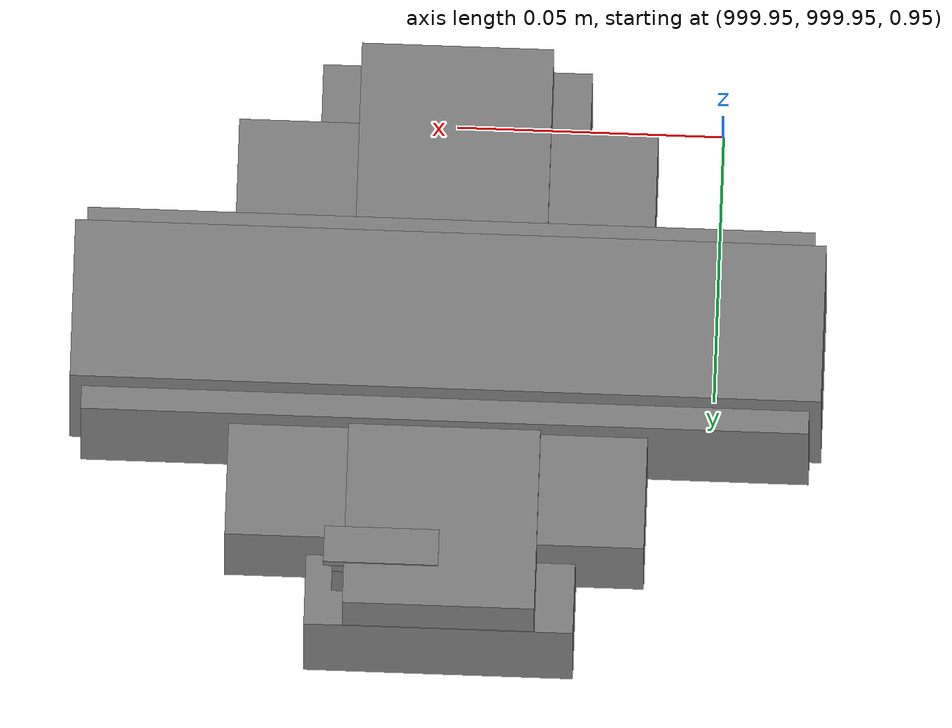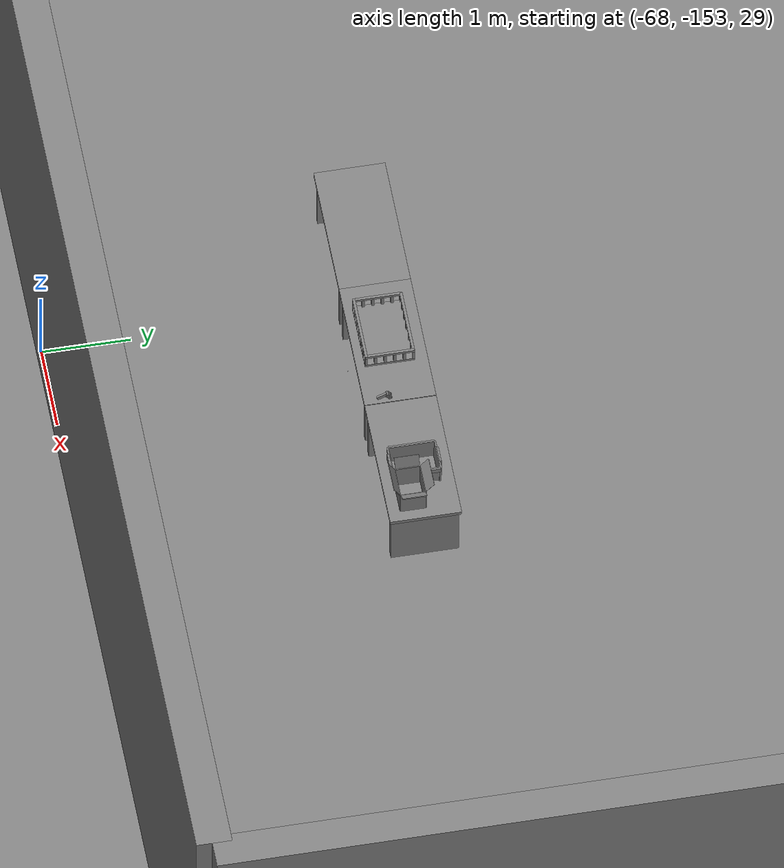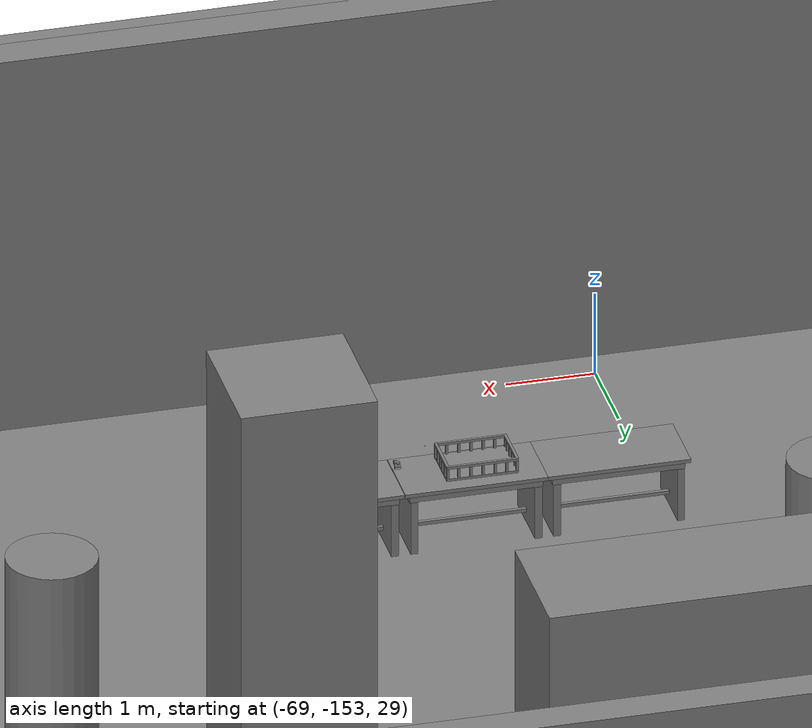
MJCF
<mujoco>
    <option gravity="0.000000000 0.000000000 -9.810000420" timestep="0.0049999999" integrator="implicitfast" density="1.225" viscosity="1.8000001e-05" noslip_iterations="10" iterations="100" sdf_iterations="50">
        <flag multiccd="disable"/>
    </option>
    <size memory="1000M"/>
    <compiler coordinate="local"/>
    <worldbody>
        <light cutoff="30" pos="0 1 1" dir="0 -1 -2"/>
        <light cutoff="30" pos="0 -1 1" dir="0 1 -2"/>
        <body pos="1000.000000000 1000.000000000 1.000000000" euler="0.000000000 0.000000000 180.000000000" name="openloong_gripper_2f85_fix_base_usda_wifi_box">
            <geom contype="1" conaffinity="1" density="1000" type="box" material="" rgba="0.500000000 0.500000000 0.500000000 1.000000000" solimp="0.899999976 0.949999988 0.001000000" friction="1.000000000 0.005000000 0.000100000" solref="0.020000000 1.000000000" margin="0" condim="3" group="0" pos="0.000000000 0.000000000 0.058978677" quat="0.000000000 0.000000047 0.000000000 1.000000000" size="0.068499997 0.018999999 0.059000000" name="openloong_gripper_2f85_fix_base_usda_geom_665AFFA5_B4C3_4311_9157_C0F2254B3235"/>
            <freejoint name="openloong_gripper_2f85_fix_base_usda_wifi_box_joint"/>
            <site size="0.005000000 0.005000000 0.005000000" rgba="0.500000000 0.500000000 0.500000000 1.000000000" pos="0.000000000 0.000000000 0.000000000" quat="0.999961913 0.008726500 0.000000000 0.000000000" group="0" type="sphere" name="openloong_gripper_2f85_fix_base_usda_wifi_boxsite"/>
        </body>
        <body pos="-66.195404053 -149.544815063 31.171390533" euler="164.780059814 -18.541301727 163.928451538" mocap="true" name="spotlight3_SpotLight"/>
        <body pos="1000.000000000 999.999938965 1.000000000" euler="0.000000000 0.000000000 180.000000000" name="openloong_gripper_2f85_fix_base_usda_intelcore_i5">
            <geom contype="1" conaffinity="1" density="1000" type="box" material="" rgba="0.500000000 0.500000000 0.500000000 1.000000000" solimp="0.899999976 0.949999988 0.001000000" friction="1.000000000 0.005000000 0.000100000" solref="0.020000000 1.000000000" margin="0" condim="3" group="0" pos="0.000000000 0.000000000 0.051722717" quat="0.707106709 0.000000000 0.000000000 -0.707106769" size="0.052800000 0.018080002 0.052800000" name="openloong_gripper_2f85_fix_base_usda_geom_493E1977_C5FE_4220_94DF_874327BA4965"/>
            <freejoint name="openloong_gripper_2f85_fix_base_usda_intelcore_i5_joint"/>
            <site size="0.005000000 0.005000000 0.005000000" rgba="0.500000000 0.500000000 0.500000000 1.000000000" pos="0.000000000 0.000000000 0.000000000" quat="0.999961913 0.008726534 0.000000000 0.000000000" group="0" type="sphere" name="openloong_gripper_2f85_fix_base_usda_intelcore_i5site"/>
        </body>
        <body pos="1000.000000000 1000.000000000 1.000000000" euler="0.000000000 0.000000000 180.000000000" name="openloong_gripper_2f85_fix_base_usda_battery_01">
            <geom contype="1" conaffinity="1" density="1000" type="box" material="" rgba="0.500000000 0.500000000 0.500000000 1.000000000" solimp="0.899999976 0.949999988 0.001000000" friction="1.000000000 0.005000000 0.000100000" solref="0.020000000 1.000000000" margin="0" condim="3" group="0" pos="-0.011123657 -0.041940309 0.101691343" quat="1.000000000 0.000000000 0.000000000 0.000000000" size="0.010800000 0.003375000 0.004725000" name="openloong_gripper_2f85_fix_base_usda_geom_00806FF7_D2DC_4EEA_B904_86101AB0CEEA"/>
            <geom contype="1" conaffinity="1" density="1000" type="box" material="" rgba="0.500000000 0.500000000 0.500000000 1.000000000" solimp="0.899999976 0.949999988 0.001000000" friction="1.000000000 0.005000000 0.000100000" solref="0.020000000 1.000000000" margin="0" condim="3" group="0" pos="-0.010876465 -0.044247437 0.047066893" quat="0.998702705 -0.050920475 0.000000000 0.000000000" size="0.009450001 0.002700000 0.024975000" name="openloong_gripper_2f85_fix_base_usda_geom_471348E3_CD67_4ABD_82C0_24BCEC3AA286"/>
            <geom contype="1" conaffinity="1" density="1000" type="box" material="" rgba="0.500000000 0.500000000 0.500000000 1.000000000" solimp="0.899999976 0.949999988 0.001000000" friction="1.000000000 0.005000000 0.000100000" solref="0.020000000 1.000000000" margin="0" condim="3" group="0" pos="-0.001235962 -0.000659180 0.047381196" quat="1.000000000 0.000000000 0.000000000 0.000000000" size="0.039420001 0.039150000 0.047250003" name="openloong_gripper_2f85_fix_base_usda_geom_F91B8442_C412_435D_A506_700786904288"/>
            <geom contype="1" conaffinity="1" density="1000" type="box" material="" rgba="0.500000000 0.500000000 0.500000000 1.000000000" solimp="0.899999976 0.949999988 0.001000000" friction="1.000000000 0.005000000 0.000100000" solref="0.020000000 1.000000000" margin="0" condim="3" group="0" pos="-0.010876465 -0.039138794 0.009851727" quat="1.000000000 0.000000000 0.000000000 0.000000000" size="0.009450001 0.010800000 0.013500000" name="openloong_gripper_2f85_fix_base_usda_geom_3F648F48_4869_44F7_8A34_1E6605833D96"/>
            <geom contype="1" conaffinity="1" density="1000" type="box" material="" rgba="0.500000000 0.500000000 0.500000000 1.000000000" solimp="0.899999976 0.949999988 0.001000000" friction="1.000000000 0.005000000 0.000100000" solref="0.020000000 1.000000000" margin="0" condim="3" group="0" pos="-0.010876465 -0.041528322 0.071508206" quat="1.000000000 0.000000000 0.000000000 0.000000000" size="0.009450001 0.002700000 0.027000001" name="openloong_gripper_2f85_fix_base_usda_geom_A0A886FD_68A1_4CCA_B403_F9DEFAE67CC5"/>
            <freejoint name="openloong_gripper_2f85_fix_base_usda_battery_01_joint"/>
            <site size="0.005000000 0.005000000 0.005000000" rgba="0.500000000 0.500000000 0.500000000 1.000000000" pos="0.000000000 0.000000000 0.000000000" quat="0.999961913 0.008726500 0.000000000 0.000000000" group="0" type="sphere" name="openloong_gripper_2f85_fix_base_usda_battery_01site"/>
        </body>
        <body pos="1000.000000000 1000.000000000 1.000000000" euler="0.000000000 0.000000000 180.000000000" name="openloong_gripper_2f85_fix_base_usda_cpu_fan">
            <geom contype="1" conaffinity="1" density="1000" type="box" material="" rgba="0.500000000 0.500000000 0.500000000 1.000000000" solimp="0.899999976 0.949999988 0.001000000" friction="1.000000000 0.005000000 0.000100000" solref="0.020000000 1.000000000" margin="0" condim="3" group="0" pos="0.000000000 0.000000000 0.070034981" quat="0.000000000 0.000000000 0.000000000 1.000000000" size="0.070700005 0.014699999 0.070700005" name="openloong_gripper_2f85_fix_base_usda_geom_4046C7D5_A546_4DAC_B51D_6D4D2DC24CE0"/>
            <freejoint name="openloong_gripper_2f85_fix_base_usda_cpu_fan_joint"/>
            <site size="0.005000000 0.005000000 0.005000000" rgba="0.500000000 0.500000000 0.500000000 1.000000000" pos="0.000000000 0.000000000 0.000000000" quat="0.999961913 0.008726535 0.000000000 0.000000000" group="0" type="sphere" name="openloong_gripper_2f85_fix_base_usda_cpu_fancsite"/>
        </body>
        <body pos="1000.000000000 1000.000000000 1.000000000" euler="0.000011953 0.000005123 -179.999984741" name="openloong_gripper_2f85_fix_base_usda_intel_box">
            <geom contype="1" conaffinity="1" density="1000" type="box" material="" rgba="0.500000000 0.500000000 0.500000000 1.000000000" solimp="0.899999976 0.949999988 0.001000000" friction="1.000000000 0.005000000 0.000100000" solref="0.020000000 1.000000000" margin="0" condim="3" group="0" pos="0.000000000 -0.000067139 0.000082284" quat="0.707106709 0.000000225 0.000000253 0.707106650" size="0.052800003 0.025300000 0.052800003" name="openloong_gripper_2f85_fix_base_usda_geom_1C1E5B44_F58F_4EE6_82C1_B2CD3F9C9680"/>
            <freejoint name="openloong_gripper_2f85_fix_base_usda_intel_box_joint"/>
            <site size="0.005000000 0.005000000 0.005000000" rgba="0.500000000 0.500000000 0.500000000 1.000000000" pos="0.000000000 0.000000000 0.000000000" quat="0.999961913 0.008726500 0.000000000 0.000000000" group="0" type="sphere" name="openloong_gripper_2f85_fix_base_usda_intel_boxsite"/>
        </body>
        <body pos="-66.371040344 -148.844787598 31.169418335" euler="0.716806829 12.745818138 44.492755890" mocap="true" name="spotlight5_SpotLight"/>
        <body pos="-65.940223694 -148.893600464 31.166822433" euler="131.456359863 -43.138622284 170.384033203" mocap="true" name="spotlight4_SpotLight"/>
        <body pos="-64.866622925 -149.383972168 30.183746338" euler="89.999984741 89.999946594 0.000000000" name="openloong_gripper_2f85_fix_base_usda_bluebox_01">
            <geom contype="1" conaffinity="1" density="1000" type="box" material="" rgba="0.500000000 0.500000000 0.500000000 1.000000000" solimp="0.899999976 0.949999988 0.001000000" friction="1.000000000 0.005000000 0.000100000" solref="0.020000000 1.000000000" margin="0" condim="3" group="0" pos="0.276580811 0.187225342 0.000068665" quat="0.707106948 0.000077471 0.707106352 0.000077486" size="0.100000001 0.057999998 0.010000000" name="openloong_gripper_2f85_fix_base_usda_geom_564FEE0E_40F6_4651_84C9_106340A606C3"/>
            <geom contype="1" conaffinity="1" density="1000" type="box" material="" rgba="0.500000000 0.500000000 0.500000000 1.000000000" solimp="0.899999976 0.949999988 0.001000000" friction="1.000000000 0.005000000 0.000100000" solref="0.020000000 1.000000000" margin="0" condim="3" group="0" pos="0.000000000 0.002883911 0.000000000" quat="0.999999881 0.000000000 0.000000000 0.000000000" size="0.254000008 0.003000000 0.172000006" name="openloong_gripper_2f85_fix_base_usda_geom_FA648EC9_ED0F_4266_BAD4_55EEC2EDCCC6"/>
            <geom contype="1" conaffinity="1" density="1000" type="box" material="" rgba="0.500000000 0.500000000 0.500000000 1.000000000" solimp="0.899999976 0.949999988 0.001000000" friction="1.000000000 0.005000000 0.000100000" solref="0.020000000 1.000000000" margin="0" condim="3" group="0" pos="0.000000000 0.124874115 0.173484802" quat="0.999796331 0.020176515 -0.000000015 0.000000030" size="0.259999990 0.119999997 0.007000000" name="openloong_gripper_2f85_fix_base_usda_geom_CCF51D7D_2F3E_4B4B_ABB9_7A9A3E3275BC"/>
            <geom contype="1" conaffinity="1" density="1000" type="box" material="" rgba="0.500000000 0.500000000 0.500000000 1.000000000" solimp="0.899999976 0.949999988 0.001000000" friction="1.000000000 0.005000000 0.000100000" solref="0.020000000 1.000000000" margin="0" condim="3" group="0" pos="0.000000000 0.124874115 -0.173469543" quat="0.999796331 -0.020176545 -0.000000015 0.000000000" size="0.259999990 0.119999997 0.007000000" name="openloong_gripper_2f85_fix_base_usda_geom_C678990D_C7E5_4E5D_9E15_417495C52464"/>
            <geom contype="1" conaffinity="1" density="1000" type="box" material="" rgba="0.500000000 0.500000000 0.500000000 1.000000000" solimp="0.899999976 0.949999988 0.001000000" friction="1.000000000 0.005000000 0.000100000" solref="0.020000000 1.000000000" margin="0" condim="3" group="0" pos="0.000000000 0.214008331 0.188980103" quat="0.999912977 0.013176724 0.000000015 0.000000000" size="0.259999990 0.029999999 0.012500000" name="openloong_gripper_2f85_fix_base_usda_geom_C87268D7_2C23_4BBB_966C_6FA43792BC68"/>
            <geom contype="1" conaffinity="1" density="1000" type="box" material="" rgba="0.500000000 0.500000000 0.500000000 1.000000000" solimp="0.899999976 0.949999988 0.001000000" friction="1.000000000 0.005000000 0.000100000" solref="0.020000000 1.000000000" margin="0" condim="3" group="0" pos="-0.258361816 0.125289917 0.001876831" quat="0.702796936 -0.020792112 0.710783124 0.020769298" size="0.189999998 0.119999997 0.009000000" name="openloong_gripper_2f85_fix_base_usda_geom_5CDAC6E8_F457_4349_B148_5A181F716DF8"/>
            <geom contype="1" conaffinity="1" density="1000" type="box" material="" rgba="0.500000000 0.500000000 0.500000000 1.000000000" solimp="0.899999976 0.949999988 0.001000000" friction="1.000000000 0.005000000 0.000100000" solref="0.020000000 1.000000000" margin="0" condim="3" group="0" pos="0.000000000 0.214008331 -0.188980103" quat="0.999912977 -0.013176769 0.000000030 0.000000015" size="0.259999990 0.029999999 0.012500000" name="openloong_gripper_2f85_fix_base_usda_geom_043237DC_C1AA_493C_8C01_DEC1851CC0E8"/>
            <geom contype="1" conaffinity="1" density="1000" type="box" material="" rgba="0.500000000 0.500000000 0.500000000 1.000000000" solimp="0.899999976 0.949999988 0.001000000" friction="1.000000000 0.005000000 0.000100000" solref="0.020000000 1.000000000" margin="0" condim="3" group="0" pos="-0.276611328 0.187225342 0.000068665" quat="0.707106650 0.000077441 0.707106709 0.000077456" size="0.100000001 0.057999998 0.010000000" name="openloong_gripper_2f85_fix_base_usda_geom_B170AF73_4F42_42BB_A6F3_6FDBF34971E2"/>
            <geom contype="1" conaffinity="1" density="1000" type="box" material="" rgba="0.500000000 0.500000000 0.500000000 1.000000000" solimp="0.899999976 0.949999988 0.001000000" friction="1.000000000 0.005000000 0.000100000" solref="0.020000000 1.000000000" margin="0" condim="3" group="0" pos="0.258331299 0.125289917 0.001876831" quat="0.702851415 0.018856421 0.710823774 -0.019329369" size="0.189999998 0.119999997 0.009000000" name="openloong_gripper_2f85_fix_base_usda_geom_D9F470D3_E278_4A95_8078_7FBFBE5C46B4"/>
            <freejoint name="openloong_gripper_2f85_fix_base_usda_bluebox_01_joint"/>
            <site size="0.005000000 0.005000000 0.005000000" rgba="0.500000000 0.500000000 0.500000000 1.000000000" pos="0.000000000 0.000000000 0.000000000" quat="0.999961913 0.008726534 0.000000000 0.000000000" group="0" type="sphere" name="openloong_gripper_2f85_fix_base_usda_bluebox_01site"/>
        </body>
        <body pos="-64.496299744 -149.491867065 30.235729218" euler="0.000000000 0.000000000 89.999946594" name="openloong_gripper_2f85_fix_base_usda_cardboardbox_01">
            <geom contype="1" conaffinity="1" density="1000" type="box" material="" rgba="0.500000000 0.500000000 0.500000000 1.000000000" solimp="0.899999976 0.949999988 0.001000000" friction="1.000000000 0.005000000 0.000100000" solref="0.020000000 1.000000000" margin="0" condim="3" group="0" pos="-0.003166199 -0.004086494 0.005052090" quat="1.000000000 0.000000000 0.000000000 0.000000000" size="0.142499998 0.177500010 0.005000000" name="openloong_gripper_2f85_fix_base_usda_geom_4A096C6C_3E7E_4B08_B706_E7D0ED49B4C4"/>
            <geom contype="1" conaffinity="1" density="1000" type="box" material="" rgba="0.500000000 0.500000000 0.500000000 1.000000000" solimp="0.899999976 0.949999988 0.001000000" friction="1.000000000 0.005000000 0.000100000" solref="0.020000000 1.000000000" margin="0" condim="3" group="0" pos="-0.003166199 0.170316696 0.150570869" quat="1.000000000 0.000000000 0.000000000 0.000000000" size="0.142499998 0.005000000 0.149999991" name="openloong_gripper_2f85_fix_base_usda_geom_08702019_448D_4A2E_BD56_10E9A130786D"/>
            <geom contype="1" conaffinity="1" density="1000" type="box" material="" rgba="0.500000000 0.500000000 0.500000000 1.000000000" solimp="0.899999976 0.949999988 0.001000000" friction="1.000000000 0.005000000 0.000100000" solref="0.020000000 1.000000000" margin="0" condim="3" group="0" pos="-0.147399902 -0.005307198 0.150570869" quat="1.000000000 0.000000000 0.000000000 0.000000000" size="0.005000000 0.177500010 0.149999991" name="openloong_gripper_2f85_fix_base_usda_geom_4225FC13_8A52_4A0B_B153_6A20A72F4080"/>
            <geom contype="1" conaffinity="1" density="1000" type="box" material="" rgba="0.500000000 0.500000000 0.500000000 1.000000000" solimp="0.899999976 0.949999988 0.001000000" friction="1.000000000 0.005000000 0.000100000" solref="0.020000000 1.000000000" margin="0" condim="3" group="0" pos="0.140275955 -0.005307198 0.150570869" quat="1.000000000 0.000000000 0.000000000 0.000000000" size="0.005000000 0.177500010 0.149999991" name="openloong_gripper_2f85_fix_base_usda_geom_CF289451_5833_4043_AA6A_9E260648677A"/>
            <geom contype="1" conaffinity="1" density="1000" type="box" material="" rgba="0.500000000 0.500000000 0.500000000 1.000000000" solimp="0.899999976 0.949999988 0.001000000" friction="1.000000000 0.005000000 0.000100000" solref="0.020000000 1.000000000" margin="0" condim="3" group="0" pos="-0.003166199 -0.181550980 0.150570869" quat="1.000000000 0.000000000 0.000000000 0.000000000" size="0.142499998 0.005000000 0.149999991" name="openloong_gripper_2f85_fix_base_usda_geom_27776911_344D_4FB4_A0A5_869C4E0A07AD"/>
            <freejoint name="openloong_gripper_2f85_fix_base_usda_cardboardbox_01_joint"/>
            <site size="0.005000000 0.005000000 0.005000000" rgba="0.500000000 0.500000000 0.500000000 1.000000000" pos="0.000000000 0.000000000 0.000000000" quat="0.999961913 0.008726535 0.000000000 0.000000000" group="0" type="sphere" name="openloong_gripper_2f85_fix_base_usda_site_B5D81648_BEDD_4633_8CD6_1A0CCB776C3D"/>
            <body pos="0.139160156 -0.004048347 0.301930904" euler="-179.999954224 49.383502960 179.999954224" name="openloong_gripper_2f85_fix_base_usda_A1_006">
                <geom contype="1" conaffinity="1" density="1000" type="box" material="" rgba="0.500000000 0.500000000 0.500000000 1.000000000" solimp="0.899999976 0.949999988 0.001000000" friction="1.000000000 0.005000000 0.000100000" solref="0.020000000 1.000000000" margin="0" condim="3" group="0" pos="-0.071587563 0.000009537 0.001745224" quat="0.999999881 0.000000000 0.000000000 0.000000000" size="0.071249999 0.179999992 0.002500000" name="openloong_gripper_2f85_fix_base_usda_geom_4103E133_0424_42B5_9795_E8B6D8A0A23C"/>
                <joint armature="0" stiffness="0.07" damping="0.0099999998" axis="0.000000 1.000000 0.000000" type="hinge" name="openloong_gripper_2f85_fix_base_usda_A1_006"/>
            </body>
            <body pos="-0.145902634 -0.004086494 0.301938057" euler="-180.000000000 -60.000011444 -180.000000000" name="openloong_gripper_2f85_fix_base_usda_A2_006">
                <geom contype="1" conaffinity="1" density="1000" type="box" material="" rgba="0.500000000 0.500000000 0.500000000 1.000000000" solimp="0.899999976 0.949999988 0.001000000" friction="1.000000000 0.005000000 0.000100000" solref="0.020000000 1.000000000" margin="0" condim="3" group="0" pos="0.071268082 0.000009537 0.002717972" quat="0.000002921 0.000000000 -0.000000030 0.999999881" size="0.071249999 0.179999992 0.002500000" name="openloong_gripper_2f85_fix_base_usda_geom_482DD949_A646_47C6_95D1_D2A5F964675B"/>
                <joint armature="0" stiffness="0.07" damping="0.0099999998" axis="0.000000 1.000000 0.000000" type="hinge" name="openloong_gripper_2f85_fix_base_usda_A2_006"/>
            </body>
            <body pos="-0.003385544 0.175991058 0.301930904" euler="-125.858116150 -0.000004561 0.000002331" name="openloong_gripper_2f85_fix_base_usda_B2_006">
                <geom contype="1" conaffinity="1" density="1000" type="box" material="" rgba="0.500000000 0.500000000 0.500000000 1.000000000" solimp="0.899999976 0.949999988 0.001000000" friction="1.000000000 0.005000000 0.000100000" solref="0.020000000 1.000000000" margin="0" condim="3" group="0" pos="0.000009537 -0.070939064 -0.002470016" quat="0.999614120 0.027776197 -0.000000015 0.000000030" size="0.137500003 0.064999998 0.005000000" name="openloong_gripper_2f85_fix_base_usda_geom_AD95B1F3_C636_4520_9388_F51365BC5211"/>
                <joint armature="0" stiffness="0.07" damping="0.0099999998" axis="1.000000 0.000000 0.000000" type="hinge" name="openloong_gripper_2f85_fix_base_usda_B2_006"/>
            </body>
            <body pos="-0.003385544 -0.184140205 0.301938057" euler="147.805557251 0.000000000 0.000000000" name="openloong_gripper_2f85_fix_base_usda_B1_006">
                <geom contype="1" conaffinity="1" density="1000" type="box" material="" rgba="0.500000000 0.500000000 0.500000000 1.000000000" solimp="0.899999976 0.949999988 0.001000000" friction="1.000000000 0.005000000 0.000100000" solref="0.020000000 1.000000000" margin="0" condim="3" group="0" pos="-0.000028610 0.070202351 -0.002703667" quat="0.999614179 -0.027776167 0.000000000 0.000000000" size="0.137500003 0.064999998 0.005000000" name="openloong_gripper_2f85_fix_base_usda_geom_FA3ECFC7_668F_4197_8295_3F3C3BE6FA5B"/>
                <joint armature="0" stiffness="0.07" damping="0.0099999998" axis="1.000000 0.000000 0.000000" type="hinge" name="openloong_gripper_2f85_fix_base_usda_B1_006"/>
            </body>
        </body>
        <body pos="-65.882858276 -149.481979370 30.229999542" euler="-64.487716675 0.000000000 0.000000000" name="openloong_gripper_2f85_fix_base_usda_Barcode">
            <geom contype="1" conaffinity="1" density="1000" type="box" material="" rgba="0.500000000 0.500000000 0.500000000 1.000000000" solimp="0.899999976 0.949999988 0.001000000" friction="1.000000000 0.005000000 0.000100000" solref="0.020000000 1.000000000" margin="0" condim="3" group="0" pos="0.000000000 0.013038635 0.001419067" quat="0.000000000 0.000000000 0.000000000 1.000000119" size="0.034000002 0.010000000 0.017999999" name="openloong_gripper_2f85_fix_base_usda_geom_AF770C0E_4E2D_45A5_8DBB_C5B45E875D19"/>
            <geom contype="1" conaffinity="1" density="1000" type="box" material="" rgba="0.500000000 0.500000000 0.500000000 1.000000000" solimp="0.899999976 0.949999988 0.001000000" friction="1.000000000 0.005000000 0.000100000" solref="0.020000000 1.000000000" margin="0" condim="3" group="0" pos="0.000000000 -0.035301208 -0.007095337" quat="0.000000000 0.000000000 -0.043619365 0.999048233" size="0.028999999 0.010000000 0.020000000" name="openloong_gripper_2f85_fix_base_usda_geom_DB11414E_2630_4A1F_96BD_89C9E57DEF5A"/>
            <geom contype="1" conaffinity="1" density="1000" type="box" material="" rgba="0.500000000 0.500000000 0.500000000 1.000000000" solimp="0.899999976 0.949999988 0.001000000" friction="1.000000000 0.005000000 0.000100000" solref="0.020000000 1.000000000" margin="0" condim="3" group="0" pos="0.000000000 -0.043411255 -0.011749268" quat="0.922262907 0.386563420 0.000000000 0.000000000" size="0.026000001 0.010000000 0.020000000" name="openloong_gripper_2f85_fix_base_usda_geom_4A8E7243_B73D_4FD1_A332_157C88D76183"/>
            <geom contype="1" conaffinity="1" density="1000" type="box" material="" rgba="0.500000000 0.500000000 0.500000000 1.000000000" solimp="0.899999976 0.949999988 0.001000000" friction="1.000000000 0.005000000 0.000100000" solref="0.020000000 1.000000000" margin="0" condim="3" group="0" pos="0.000000000 -0.016967773 -0.031860352" quat="0.000000000 0.000000000 0.000000000 1.000000119" size="0.008000000 0.010000000 0.013000000" name="openloong_gripper_2f85_fix_base_usda_geom_0733AE3F_2933_4CDD_99AB_E032ADC4519B"/>
            <geom contype="1" conaffinity="1" density="1000" type="box" material="" rgba="0.500000000 0.500000000 0.500000000 1.000000000" solimp="0.899999976 0.949999988 0.001000000" friction="1.000000000 0.005000000 0.000100000" solref="0.020000000 1.000000000" margin="0" condim="3" group="0" pos="0.000000000 -0.001869202 0.000312805" quat="0.953716993 0.300705761 0.000000000 0.000000000" size="0.032000002 0.010000000 0.018999999" name="openloong_gripper_2f85_fix_base_usda_geom_DF78F73B_EA3F_4F05_92ED_0B069C034AA0"/>
            <geom contype="1" conaffinity="1" density="1000" type="box" material="" rgba="0.500000000 0.500000000 0.500000000 1.000000000" solimp="0.899999976 0.949999988 0.001000000" friction="1.000000000 0.005000000 0.000100000" solref="0.020000000 1.000000000" margin="0" condim="3" group="0" pos="0.000000000 -0.019531250 -0.003173828" quat="0.953716993 0.300705761 0.000000000 0.000000000" size="0.030999999 0.010000000 0.020000000" name="openloong_gripper_2f85_fix_base_usda_geom_372F865C_234D_4E8E_94E2_F193A234D39A"/>
            <geom contype="1" conaffinity="1" density="1000" type="box" material="" rgba="0.500000000 0.500000000 0.500000000 1.000000000" solimp="0.899999976 0.949999988 0.001000000" friction="1.000000000 0.005000000 0.000100000" solref="0.020000000 1.000000000" margin="0" condim="3" group="0" pos="0.000000000 -0.035301208 -0.007095337" quat="0.953716993 0.300705761 0.000000000 0.000000000" size="0.028999999 0.010000000 0.020000000" name="openloong_gripper_2f85_fix_base_usda_geom_B65D9D29_7806_40C4_8BCC_5BCEA56169EE"/>
            <geom contype="1" conaffinity="1" density="1000" type="box" material="" rgba="0.500000000 0.500000000 0.500000000 1.000000000" solimp="0.899999976 0.949999988 0.001000000" friction="1.000000000 0.005000000 0.000100000" solref="0.020000000 1.000000000" margin="0" condim="3" group="0" pos="0.000000000 -0.042617798 -0.071121216" quat="0.000000000 0.000000000 0.000000000 1.000000119" size="0.013000000 0.021000000 0.059999999" name="openloong_gripper_2f85_fix_base_usda_geom_FF778B96_FEF7_4D06_8842_7BFE086E5DC6"/>
            <freejoint name="openloong_gripper_2f85_fix_base_usda_Barcode_joint"/>
            <site size="0.005000000 0.005000000 0.005000000" rgba="0.500000000 0.500000000 0.500000000 1.000000000" pos="0.000000000 0.000000000 0.000000000" quat="1.000000000 0.000000000 0.000000000 0.000000000" group="0" type="sphere" name="openloong_gripper_2f85_fix_base_usda_Barcode_site"/>
        </body>
        <body pos="-66.745018005 -149.392349243 30.184000015" euler="0.000000000 0.000000000 89.999946594" name="[22330561351124]_Basket_01">
            <geom contype="1" conaffinity="1" density="1000" type="box" material="" rgba="0.500000000 0.500000000 0.500000000 1.000000000" solimp="0.899999976 0.949999988 0.001000000" friction="1.000000000 0.005000000 0.000100000" solref="0.020000000 1.000000000" margin="0" condim="3" group="0" pos="-0.052425385 0.389207840 0.089787483" quat="0.707107008 0.000000000 0.000000000 0.707106411" size="0.014249999 0.014249999 0.059999999" name="[22330561351124]_geom_1009A3D1_2016_4B64_B13D_C2126C43D7DA"/>
            <geom contype="1" conaffinity="1" density="1000" type="box" material="" rgba="0.500000000 0.500000000 0.500000000 1.000000000" solimp="0.899999976 0.949999988 0.001000000" friction="1.000000000 0.005000000 0.000100000" solref="0.020000000 1.000000000" margin="0" condim="3" group="0" pos="0.264015198 -0.133043289 0.089787483" quat="0.707107008 0.000000000 0.000000000 0.707106411" size="0.014249999 0.014249999 0.059999999" name="[22330561351124]_geom_587AF9FD_288A_4CE0_9312_CBFA0F3308AD"/>
            <geom contype="1" conaffinity="1" density="1000" type="box" material="" rgba="0.500000000 0.500000000 0.500000000 1.000000000" solimp="0.899999976 0.949999988 0.001000000" friction="1.000000000 0.005000000 0.000100000" solref="0.020000000 1.000000000" margin="0" condim="3" group="0" pos="-0.264015198 -0.265548706 0.089793205" quat="0.707107008 0.000000000 0.000000000 0.707106411" size="0.014249999 0.014249999 0.059999999" name="[22330561351124]_geom_2540A23E_A8A2_431A_B462_1621A76006C2"/>
            <geom contype="1" conaffinity="1" density="1000" type="box" material="" rgba="0.500000000 0.500000000 0.500000000 1.000000000" solimp="0.899999976 0.949999988 0.001000000" friction="1.000000000 0.005000000 0.000100000" solref="0.020000000 1.000000000" margin="0" condim="3" group="0" pos="-0.160263062 -0.389322281 0.089793205" quat="0.707107008 0.000000000 0.000000000 0.707106411" size="0.014249999 0.014249999 0.059999999" name="[22330561351124]_geom_FF6255B9_14EC_4972_BC34_2A2158617BD9"/>
            <geom contype="1" conaffinity="1" density="1000" type="box" material="" rgba="0.500000000 0.500000000 0.500000000 1.000000000" solimp="0.899999976 0.949999988 0.001000000" friction="1.000000000 0.005000000 0.000100000" solref="0.020000000 1.000000000" margin="0" condim="3" group="0" pos="0.162265778 -0.389322281 0.089787483" quat="0.707107008 0.000000000 0.000000000 0.707106411" size="0.014249999 0.014249999 0.059999999" name="[22330561351124]_geom_930EDE13_912F_4759_9EF5_4F9F0731C07B"/>
            <geom contype="1" conaffinity="1" density="1000" type="box" material="" rgba="0.500000000 0.500000000 0.500000000 1.000000000" solimp="0.899999976 0.949999988 0.001000000" friction="1.000000000 0.005000000 0.000100000" solref="0.020000000 1.000000000" margin="0" condim="3" group="0" pos="0.264015198 0.389207840 0.089787483" quat="0.707107008 0.000000000 0.000000000 0.707106411" size="0.014249999 0.014249999 0.059999999" name="[22330561351124]_geom_C97423EB_1ABF_4CDB_BB75_1FE827C8C3B7"/>
            <geom contype="1" conaffinity="1" density="1000" type="box" material="" rgba="0.500000000 0.500000000 0.500000000 1.000000000" solimp="0.899999976 0.949999988 0.001000000" friction="1.000000000 0.005000000 0.000100000" solref="0.020000000 1.000000000" margin="0" condim="3" group="0" pos="-0.264015198 -0.133043289 0.089793205" quat="0.707107008 0.000000000 0.000000000 0.707106411" size="0.014249999 0.014249999 0.059999999" name="[22330561351124]_geom_4983810D_3846_415A_A008_0F7F6C7934E3"/>
            <geom contype="1" conaffinity="1" density="1000" type="box" material="" rgba="0.500000000 0.500000000 0.500000000 1.000000000" solimp="0.899999976 0.949999988 0.001000000" friction="1.000000000 0.005000000 0.000100000" solref="0.020000000 1.000000000" margin="0" condim="3" group="0" pos="-0.264026642 0.269256592 0.089793205" quat="0.707107008 0.000000000 0.000000000 0.707106411" size="0.014249999 0.014249999 0.059999999" name="[22330561351124]_geom_7034505E_A73B_43DA_9D27_4AF2CCA67EB2"/>
            <geom contype="1" conaffinity="1" density="1000" type="box" material="" rgba="0.500000000 0.500000000 0.500000000 1.000000000" solimp="0.899999976 0.949999988 0.001000000" friction="1.000000000 0.005000000 0.000100000" solref="0.020000000 1.000000000" margin="0" condim="3" group="0" pos="0.054462433 0.389207840 0.089787483" quat="0.707107008 0.000000000 0.000000000 0.707106411" size="0.014249999 0.014249999 0.059999999" name="[22330561351124]_geom_D0CBC240_557D_45A8_B175_E67955A45A5B"/>
            <geom contype="1" conaffinity="1" density="1000" type="box" material="" rgba="0.500000000 0.500000000 0.500000000 1.000000000" solimp="0.899999976 0.949999988 0.001000000" friction="1.000000000 0.005000000 0.000100000" solref="0.020000000 1.000000000" margin="0" condim="3" group="0" pos="0.054462433 -0.389322281 0.089787483" quat="0.707107008 0.000000000 0.000000000 0.707106411" size="0.014249999 0.014249999 0.059999999" name="[22330561351124]_geom_1ABCDED8_5D6D_41C7_9E19_62E887A53BF6"/>
            <geom contype="1" conaffinity="1" density="1000" type="box" material="" rgba="0.500000000 0.500000000 0.500000000 1.000000000" solimp="0.899999976 0.949999988 0.001000000" friction="1.000000000 0.005000000 0.000100000" solref="0.020000000 1.000000000" margin="0" condim="3" group="0" pos="0.264015198 0.269256592 0.089793205" quat="0.707107008 0.000000000 0.000000000 0.707106411" size="0.014249999 0.014249999 0.059999999" name="[22330561351124]_geom_B432EB38_A2D1_4C1E_9B9C_8E6E0F512509"/>
            <geom contype="1" conaffinity="1" density="1000" type="box" material="" rgba="0.500000000 0.500000000 0.500000000 1.000000000" solimp="0.899999976 0.949999988 0.001000000" friction="1.000000000 0.005000000 0.000100000" solref="0.020000000 1.000000000" margin="0" condim="3" group="0" pos="0.264015198 -0.389322281 0.089787483" quat="0.707107008 0.000000000 0.000000000 0.707106411" size="0.014249999 0.014249999 0.059999999" name="[22330561351124]_geom_78508413_9652_43E7_97FE_BF1453A9C7EC"/>
            <geom contype="1" conaffinity="1" density="1000" type="box" material="" rgba="0.500000000 0.500000000 0.500000000 1.000000000" solimp="0.899999976 0.949999988 0.001000000" friction="1.000000000 0.005000000 0.000100000" solref="0.020000000 1.000000000" margin="0" condim="3" group="0" pos="0.000000000 0.000000000 0.015998840" quat="0.707107008 0.000000000 0.000000000 0.707106411" size="0.403499991 0.279000014 0.015750000" name="[22330561351124]_geom_005D7851_3BA7_4BDD_A70D_51DDD9B711BE"/>
            <geom contype="1" conaffinity="1" density="1000" type="box" material="" rgba="0.500000000 0.500000000 0.500000000 1.000000000" solimp="0.899999976 0.949999988 0.001000000" friction="1.000000000 0.005000000 0.000100000" solref="0.020000000 1.000000000" margin="0" condim="3" group="0" pos="0.000000000 -0.389476776 0.163619041" quat="0.707107008 0.000000000 0.000000000 0.707106411" size="0.015000000 0.277500004 0.015750000" name="[22330561351124]_geom_2FFCAF97_2362_489C_BBDC_FC4CB8C29C93"/>
            <geom contype="1" conaffinity="1" density="1000" type="box" material="" rgba="0.500000000 0.500000000 0.500000000 1.000000000" solimp="0.899999976 0.949999988 0.001000000" friction="1.000000000 0.005000000 0.000100000" solref="0.020000000 1.000000000" margin="0" condim="3" group="0" pos="0.162265778 0.389207840 0.089787483" quat="0.707107008 0.000000000 0.000000000 0.707106411" size="0.014249999 0.014249999 0.059999999" name="[22330561351124]_geom_F33FD21E_0D15_421F_9018_2A16673ACD36"/>
            <geom contype="1" conaffinity="1" density="1000" type="box" material="" rgba="0.500000000 0.500000000 0.500000000 1.000000000" solimp="0.899999976 0.949999988 0.001000000" friction="1.000000000 0.005000000 0.000100000" solref="0.020000000 1.000000000" margin="0" condim="3" group="0" pos="0.000000000 0.389471054 0.163619041" quat="0.707107008 0.000000000 0.000000000 0.707106411" size="0.015000000 0.277500004 0.015750000" name="[22330561351124]_geom_309F7DD3_183B_43B0_A248_0C8CE1689271"/>
            <geom contype="1" conaffinity="1" density="1000" type="box" material="" rgba="0.500000000 0.500000000 0.500000000 1.000000000" solimp="0.899999976 0.949999988 0.001000000" friction="1.000000000 0.005000000 0.000100000" solref="0.020000000 1.000000000" margin="0" condim="3" group="0" pos="-0.263511658 0.000000000 0.163619041" quat="0.707107008 0.000000000 0.000000000 0.707106411" size="0.403499991 0.015000000 0.015750000" name="[22330561351124]_geom_0C062751_69F9_4766_AFF5_ABEFD3061574"/>
            <geom contype="1" conaffinity="1" density="1000" type="box" material="" rgba="0.500000000 0.500000000 0.500000000 1.000000000" solimp="0.899999976 0.949999988 0.001000000" friction="1.000000000 0.005000000 0.000100000" solref="0.020000000 1.000000000" margin="0" condim="3" group="0" pos="-0.264015198 0.141334534 0.089793205" quat="0.707107008 0.000000000 0.000000000 0.707106411" size="0.014249999 0.014249999 0.059999999" name="[22330561351124]_geom_B13C699A_55F0_494C_AC99_2B7C57908C2D"/>
            <geom contype="1" conaffinity="1" density="1000" type="box" material="" rgba="0.500000000 0.500000000 0.500000000 1.000000000" solimp="0.899999976 0.949999988 0.001000000" friction="1.000000000 0.005000000 0.000100000" solref="0.020000000 1.000000000" margin="0" condim="3" group="0" pos="0.264015198 -0.265548706 0.089787483" quat="0.707107008 0.000000000 0.000000000 0.707106411" size="0.014249999 0.014249999 0.059999999" name="[22330561351124]_geom_0A881C65_8073_4F20_B81C_575810AB313D"/>
            <geom contype="1" conaffinity="1" density="1000" type="box" material="" rgba="0.500000000 0.500000000 0.500000000 1.000000000" solimp="0.899999976 0.949999988 0.001000000" friction="1.000000000 0.005000000 0.000100000" solref="0.020000000 1.000000000" margin="0" condim="3" group="0" pos="-0.160263062 0.389207840 0.089787483" quat="0.707107008 0.000000000 0.000000000 0.707106411" size="0.014249999 0.014249999 0.059999999" name="[22330561351124]_geom_DA7DF41C_A9DC_4166_91A7_34B3A86A67E6"/>
            <geom contype="1" conaffinity="1" density="1000" type="box" material="" rgba="0.500000000 0.500000000 0.500000000 1.000000000" solimp="0.899999976 0.949999988 0.001000000" friction="1.000000000 0.005000000 0.000100000" solref="0.020000000 1.000000000" margin="0" condim="3" group="0" pos="-0.052425385 -0.389322281 0.089787483" quat="0.707107008 0.000000000 0.000000000 0.707106411" size="0.014249999 0.014249999 0.059999999" name="[22330561351124]_geom_A8544839_7A64_4413_932C_B5652EC36B1E"/>
            <geom contype="1" conaffinity="1" density="1000" type="box" material="" rgba="0.500000000 0.500000000 0.500000000 1.000000000" solimp="0.899999976 0.949999988 0.001000000" friction="1.000000000 0.005000000 0.000100000" solref="0.020000000 1.000000000" margin="0" condim="3" group="0" pos="-0.264026642 -0.389322281 0.089793205" quat="0.707107008 0.000000000 0.000000000 0.707106411" size="0.014249999 0.014249999 0.059999999" name="[22330561351124]_geom_AE381252_D87F_4B0A_9669_0967810826F2"/>
            <geom contype="1" conaffinity="1" density="1000" type="box" material="" rgba="0.500000000 0.500000000 0.500000000 1.000000000" solimp="0.899999976 0.949999988 0.001000000" friction="1.000000000 0.005000000 0.000100000" solref="0.020000000 1.000000000" margin="0" condim="3" group="0" pos="0.264015198 0.141334534 0.089787483" quat="0.707107008 0.000000000 0.000000000 0.707106411" size="0.014249999 0.014249999 0.059999999" name="[22330561351124]_geom_2ACE9C68_F482_4C84_AB8A_50CE51D7B2D3"/>
            <geom contype="1" conaffinity="1" density="1000" type="box" material="" rgba="0.500000000 0.500000000 0.500000000 1.000000000" solimp="0.899999976 0.949999988 0.001000000" friction="1.000000000 0.005000000 0.000100000" solref="0.020000000 1.000000000" margin="0" condim="3" group="0" pos="-0.264015198 0.389207840 0.089793205" quat="0.707107008 0.000000000 0.000000000 0.707106411" size="0.014249999 0.014249999 0.059999999" name="[22330561351124]_geom_4E6B5306_8726_4450_8952_C049CEEE81C1"/>
            <geom contype="1" conaffinity="1" density="1000" type="box" material="" rgba="0.500000000 0.500000000 0.500000000 1.000000000" solimp="0.899999976 0.949999988 0.001000000" friction="1.000000000 0.005000000 0.000100000" solref="0.020000000 1.000000000" margin="0" condim="3" group="0" pos="0.264015198 0.004480362 0.089787483" quat="0.707107008 0.000000000 0.000000000 0.707106411" size="0.014249999 0.014249999 0.059999999" name="[22330561351124]_geom_0D4EE23F_B560_40B5_9D73_34ED99845A6E"/>
            <geom contype="1" conaffinity="1" density="1000" type="box" material="" rgba="0.500000000 0.500000000 0.500000000 1.000000000" solimp="0.899999976 0.949999988 0.001000000" friction="1.000000000 0.005000000 0.000100000" solref="0.020000000 1.000000000" margin="0" condim="3" group="0" pos="0.263694763 -0.000011444 0.163619041" quat="0.707107008 0.000000000 0.000000000 0.707106411" size="0.403499991 0.015000000 0.015750000" name="[22330561351124]_geom_68806D32_9530_40BD_A1EF_FF28EF6A8354"/>
            <geom contype="1" conaffinity="1" density="1000" type="box" material="" rgba="0.500000000 0.500000000 0.500000000 1.000000000" solimp="0.899999976 0.949999988 0.001000000" friction="1.000000000 0.005000000 0.000100000" solref="0.020000000 1.000000000" margin="0" condim="3" group="0" pos="-0.264015198 0.004480362 0.089793205" quat="0.707107008 0.000000000 0.000000000 0.707106411" size="0.014249999 0.014249999 0.059999999" name="[22330561351124]_geom_62448396_8E16_4CF3_9E43_F9ACEF152E91"/>
            <freejoint name="[22330561351124]_joint_FB6C32F6_7CCC_4C87_99A9_632CB6FDBAA9"/>
        </body>
        <body pos="0.000000000 0.000000000 0.000000000" euler="0.000000000 0.000000000 0.000000000" name="Static Objects_Static Objects">
            <geom contype="1" conaffinity="1" density="1000" type="box" material="" rgba="0.500000000 0.500000000 0.500000000 1.000000000" solimp="0.899999976 0.949999988 0.001000000" friction="1.000000000 0.005000000 0.000100000" solref="0.020000000 1.000000000" margin="0" condim="3" group="0" pos="-67.544113159 -149.365814209 29.727830887" quat="0.500000417 0.499999970 0.499999553 0.499999970" size="0.381000012 0.319999993 0.041000001" name="Static Objects_geom_13CCD538_1710_475E_8435_0CF638BB8DF8"/>
            <geom contype="1" conaffinity="1" density="1000" type="box" material="" rgba="0.500000000 0.500000000 0.500000000 1.000000000" solimp="0.899999976 0.949999988 0.001000000" friction="1.000000000 0.005000000 0.000100000" solref="0.020000000 1.000000000" margin="0" condim="3" group="0" pos="-68.239501953 -149.365814209 30.086868286" quat="0.500000417 0.499999970 0.499999553 0.499999970" size="0.370999992 0.039500002 0.745000005" name="Static Objects_geom_0F9E1C80_1EE0_494B_AC1D_78D82F9FAA43"/>
            <geom contype="1" conaffinity="1" density="1000" type="box" material="" rgba="0.500000000 0.500000000 0.500000000 1.000000000" solimp="0.899999976 0.949999988 0.001000000" friction="1.000000000 0.005000000 0.000100000" solref="0.020000000 1.000000000" margin="0" condim="3" group="0" pos="-68.239501953 -149.365814209 30.147235870" quat="0.500000417 0.499999970 0.499999553 0.499999970" size="0.400000006 0.022000000 0.800000012" name="Static Objects_geom_C09596B1_95F3_4DA0_A9EE_BDCA4E382E93"/>
            <geom contype="1" conaffinity="1" density="1000" type="box" material="" rgba="0.500000000 0.500000000 0.500000000 1.000000000" solimp="0.899999976 0.949999988 0.001000000" friction="1.000000000 0.005000000 0.000100000" solref="0.020000000 1.000000000" margin="0" condim="3" group="0" pos="-68.934890747 -149.365814209 29.727830887" quat="0.500000417 0.499999970 0.499999553 0.499999970" size="0.381000012 0.319999993 0.041000001" name="Static Objects_geom_D5AE7BE5_D519_42E1_B491_A7982FA3539A"/>
            <geom contype="1" conaffinity="1" density="1000" type="box" material="" rgba="0.500000000 0.500000000 0.500000000 1.000000000" solimp="0.899999976 0.949999988 0.001000000" friction="1.000000000 0.005000000 0.000100000" solref="0.020000000 1.000000000" margin="0" condim="3" group="0" pos="-68.239501953 -149.365814209 29.561563492" quat="0.500000417 0.499999970 0.499999553 0.499999970" size="0.020000000 0.022000000 0.660000026" name="Static Objects_geom_A456CB3E_DD6A_4EA5_B6AA_899B8D229440"/>
            <geom contype="1" conaffinity="1" density="1000" type="box" material="" rgba="0.500000000 0.500000000 0.500000000 1.000000000" solimp="0.899999976 0.949999988 0.001000000" friction="1.000000000 0.005000000 0.000100000" solref="0.020000000 1.000000000" margin="0" condim="3" group="0" pos="-65.945671082 -149.365814209 29.727830887" quat="0.500000417 0.499999970 0.499999553 0.499999970" size="0.381000012 0.319999993 0.041000001" name="Static Objects_geom_CD2C17A1_F9E7_434D_823D_BCBD417620A1"/>
            <geom contype="1" conaffinity="1" density="1000" type="box" material="" rgba="0.500000000 0.500000000 0.500000000 1.000000000" solimp="0.899999976 0.949999988 0.001000000" friction="1.000000000 0.005000000 0.000100000" solref="0.020000000 1.000000000" margin="0" condim="3" group="0" pos="-66.641059875 -149.365814209 30.086868286" quat="0.500000417 0.499999970 0.499999553 0.499999970" size="0.370999992 0.039500002 0.745000005" name="Static Objects_geom_422B330A_3662_4FC3_8582_B8D73229A426"/>
            <geom contype="1" conaffinity="1" density="1000" type="box" material="" rgba="0.500000000 0.500000000 0.500000000 1.000000000" solimp="0.899999976 0.949999988 0.001000000" friction="1.000000000 0.005000000 0.000100000" solref="0.020000000 1.000000000" margin="0" condim="3" group="0" pos="-66.641059875 -149.365814209 30.147235870" quat="0.500000417 0.499999970 0.499999553 0.499999970" size="0.400000006 0.022000000 0.800000012" name="Static Objects_geom_7B52162A_7999_4108_992F_57B21E4A4191"/>
            <geom contype="1" conaffinity="1" density="1000" type="box" material="" rgba="0.500000000 0.500000000 0.500000000 1.000000000" solimp="0.899999976 0.949999988 0.001000000" friction="1.000000000 0.005000000 0.000100000" solref="0.020000000 1.000000000" margin="0" condim="3" group="0" pos="-67.336448669 -149.365814209 29.727830887" quat="0.500000417 0.499999970 0.499999553 0.499999970" size="0.381000012 0.319999993 0.041000001" name="Static Objects_geom_42A4C2A6_F08D_4EC0_B298_EC83F5F11B0C"/>
            <geom contype="1" conaffinity="1" density="1000" type="box" material="" rgba="0.500000000 0.500000000 0.500000000 1.000000000" solimp="0.899999976 0.949999988 0.001000000" friction="1.000000000 0.005000000 0.000100000" solref="0.020000000 1.000000000" margin="0" condim="3" group="0" pos="-66.641059875 -149.365814209 29.561563492" quat="0.500000417 0.499999970 0.499999553 0.499999970" size="0.020000000 0.022000000 0.660000026" name="Static Objects_geom_C1AEA758_56E7_4E20_9031_8B9499A36BA6"/>
            <geom contype="1" conaffinity="1" density="1000" type="box" material="" rgba="0.500000000 0.500000000 0.500000000 1.000000000" solimp="0.899999976 0.949999988 0.001000000" friction="1.000000000 0.005000000 0.000100000" solref="0.020000000 1.000000000" margin="0" condim="3" group="0" pos="-64.338577271 -149.365814209 29.727830887" quat="0.500000417 0.499999970 0.499999553 0.499999970" size="0.381000012 0.319999993 0.041000001" name="Static Objects_geom_022017D9_3BC6_483A_9F52_20C6DFE72717"/>
            <geom contype="1" conaffinity="1" density="1000" type="box" material="" rgba="0.500000000 0.500000000 0.500000000 1.000000000" solimp="0.899999976 0.949999988 0.001000000" friction="1.000000000 0.005000000 0.000100000" solref="0.020000000 1.000000000" margin="0" condim="3" group="0" pos="-65.033966064 -149.365814209 30.086868286" quat="0.500000417 0.499999970 0.499999553 0.499999970" size="0.370999992 0.039500002 0.745000005" name="Static Objects_geom_A587823A_47F1_4552_A808_89C5E12DC241"/>
            <geom contype="1" conaffinity="1" density="1000" type="box" material="" rgba="0.500000000 0.500000000 0.500000000 1.000000000" solimp="0.899999976 0.949999988 0.001000000" friction="1.000000000 0.005000000 0.000100000" solref="0.020000000 1.000000000" margin="0" condim="3" group="0" pos="-65.033966064 -149.365814209 30.147235870" quat="0.500000417 0.499999970 0.499999553 0.499999970" size="0.400000006 0.022000000 0.800000012" name="Static Objects_geom_1A0863DC_77B3_4494_BBBC_08424C1DA224"/>
            <geom contype="1" conaffinity="1" density="1000" type="box" material="" rgba="0.500000000 0.500000000 0.500000000 1.000000000" solimp="0.899999976 0.949999988 0.001000000" friction="1.000000000 0.005000000 0.000100000" solref="0.020000000 1.000000000" margin="0" condim="3" group="0" pos="-65.729354858 -149.365814209 29.727830887" quat="0.500000417 0.499999970 0.499999553 0.499999970" size="0.381000012 0.319999993 0.041000001" name="Static Objects_geom_3B82F1E4_F0D6_4D18_85B0_B3FCF7BC6BAA"/>
            <geom contype="1" conaffinity="1" density="1000" type="box" material="" rgba="0.500000000 0.500000000 0.500000000 1.000000000" solimp="0.899999976 0.949999988 0.001000000" friction="1.000000000 0.005000000 0.000100000" solref="0.020000000 1.000000000" margin="0" condim="3" group="0" pos="-65.033966064 -149.365814209 29.561563492" quat="0.500000417 0.499999970 0.499999553 0.499999970" size="0.020000000 0.022000000 0.660000026" name="Static Objects_geom_38733DA6_A5E3_43B6_B491_6C777D5E48DE"/>
            <geom contype="1" conaffinity="1" density="1000" type="box" material="" rgba="0.500000000 0.500000000 0.500000000 1.000000000" solimp="0.899999976 0.949999988 0.001000000" friction="1.000000000 0.005000000 0.000100000" solref="0.020000000 1.000000000" margin="0" condim="3" group="0" pos="-61.754566193 -137.853729248 33.906845093" quat="0.707107067 0.000000000 0.000000000 0.707106471" size="0.759999990 0.759999990 4.500000000" name="Static Objects_geom_C5BC48B9_C21A_4015_B5BD_716B53B9D4E5"/>
            <geom contype="1" conaffinity="1" density="1000" type="box" material="" rgba="0.500000000 0.500000000 0.500000000 1.000000000" solimp="0.899999976 0.949999988 0.001000000" friction="1.000000000 0.005000000 0.000100000" solref="0.020000000 1.000000000" margin="0" condim="3" group="0" pos="-57.511135101 -144.927108765 31.707921982" quat="1.000000000 0.000000000 0.000000000 0.000000000" size="0.200000003 8.000000000 2.299999952" name="Static Objects_geom_B5A8C7F3_500A_48A5_8B95_F17589B67287"/>
            <geom contype="1" conaffinity="1" density="1000" type="box" material="" rgba="0.500000000 0.500000000 0.500000000 1.000000000" solimp="0.899999976 0.949999988 0.001000000" friction="1.000000000 0.005000000 0.000100000" solref="0.020000000 1.000000000" margin="0" condim="3" group="0" pos="-80.517646790 -157.574050903 31.688196182" quat="0.707107067 0.000000000 0.000000000 0.707106471" size="0.600000024 0.600000024 2.299999952" name="Static Objects_geom_2A3071C9_8356_49D4_8EC8_367957B2824C"/>
            <geom contype="1" conaffinity="1" density="1000" type="box" material="" rgba="0.500000000 0.500000000 0.500000000 1.000000000" solimp="0.899999976 0.949999988 0.001000000" friction="1.000000000 0.005000000 0.000100000" solref="0.020000000 1.000000000" margin="0" condim="3" group="0" pos="-80.711044312 -147.414932251 31.666158676" quat="1.000000000 0.000000000 0.000000000 0.000000000" size="0.200000003 10.000000000 2.299999952" name="Static Objects_geom_3C5D955E_7341_4E8A_BDE3_AAF1A13AF7EC"/>
            <geom contype="1" conaffinity="1" density="1000" type="box" material="" rgba="0.500000000 0.500000000 0.500000000 1.000000000" solimp="0.899999976 0.949999988 0.001000000" friction="1.000000000 0.005000000 0.000100000" solref="0.020000000 1.000000000" margin="0" condim="3" group="0" pos="-57.687217712 -137.434692383 31.688196182" quat="0.707107067 0.000000000 0.000000000 0.707106471" size="0.600000024 0.600000024 2.299999952" name="Static Objects_geom_D4CE922A_E162_4076_87BD_66ED1ABCC37F"/>
            <geom contype="1" conaffinity="1" density="1000" type="box" material="" rgba="0.500000000 0.500000000 0.500000000 1.000000000" solimp="0.899999976 0.949999988 0.001000000" friction="1.000000000 0.005000000 0.000100000" solref="0.020000000 1.000000000" margin="0" condim="3" group="0" pos="-69.537033081 -140.263229370 31.714921951" quat="0.707107067 0.000000000 0.000000000 0.707106471" size="0.759999990 4.500000000 2.299999952" name="Static Objects_geom_D92440C3_3EA4_43D3_8A89_00B97E173337"/>
            <geom contype="1" conaffinity="1" density="1000" type="box" material="" rgba="0.500000000 0.500000000 0.500000000 1.000000000" solimp="0.899999976 0.949999988 0.001000000" friction="1.000000000 0.005000000 0.000100000" solref="0.020000000 1.000000000" margin="0" condim="3" group="0" pos="-80.073638916 -137.853713989 33.906845093" quat="0.707107067 0.000000000 0.000000000 0.707106471" size="0.759999990 0.759999990 4.500000000" name="Static Objects_geom_5025012D_EDAF_4CB0_AFA9_7DCF8D1EB6C9"/>
            <geom contype="1" conaffinity="1" density="1000" type="box" material="" rgba="0.500000000 0.500000000 0.500000000 1.000000000" solimp="0.899999976 0.949999988 0.001000000" friction="1.000000000 0.005000000 0.000100000" solref="0.020000000 1.000000000" margin="0" condim="3" group="0" pos="-73.406707764 -155.734664917 31.707921982" quat="1.000000000 0.000000000 0.000000000 0.000000000" size="0.200000003 3.000000000 2.299999952" name="Static Objects_geom_E8457ACF_BB31_4FE4_803A_4ADE0630530D"/>
            <geom contype="1" conaffinity="1" density="1000" type="box" material="" rgba="0.500000000 0.500000000 0.500000000 1.000000000" solimp="0.899999976 0.949999988 0.001000000" friction="1.000000000 0.005000000 0.000100000" solref="0.020000000 1.000000000" margin="0" condim="3" group="0" pos="-68.497543335 -137.448257446 31.707921982" quat="0.707107067 0.000000000 0.000000000 0.707106471" size="0.200000003 14.000000000 2.299999952" name="Static Objects_geom_12280BBA_9728_45D4_B3C9_F1003C2E8372"/>
            <geom contype="1" conaffinity="1" density="1000" type="cylinder" material="" rgba="0.500000000 0.500000000 0.500000000 1.000000000" solimp="0.899999976 0.949999988 0.001000000" friction="1.000000000 0.005000000 0.000100000" solref="0.020000000 1.000000000" margin="0" condim="3" group="0" pos="-68.868522644 -142.134506226 31.711090088" quat="0.707107067 0.000000000 0.000000000 0.707106471" size="0.509999990 2.299999952 1.000000000" name="Static Objects_geom_A8F34914_1786_4C58_A818_5928C67AFC6F"/>
            <geom contype="1" conaffinity="1" density="1000" type="plane" material="" rgba="0.500000000 0.500000000 0.500000000 1.000000000" solimp="0.899999976 0.949999988 0.001000000" friction="1.000000000 0.005000000 0.000100000" solref="0.020000000 1.000000000" margin="0" condim="3" group="0" pos="-72.873703003 -147.131927490 29.409669876" quat="1.000000000 0.000000000 0.000000000 0.000000000" size="18.000000000 14.000000000 1.000000000" name="Static Objects_geom_F9E99B74_5D25_4B20_AEC7_EE5E64F88A4A"/>
            <geom contype="1" conaffinity="1" density="1000" type="box" material="" rgba="0.500000000 0.500000000 0.500000000 1.000000000" solimp="0.899999976 0.949999988 0.001000000" friction="1.000000000 0.005000000 0.000100000" solref="0.020000000 1.000000000" margin="0" condim="3" group="0" pos="-79.943580627 -157.782272339 31.707921982" quat="0.707107067 0.000000000 0.000000000 0.707106471" size="0.200000003 7.000000000 2.299999952" name="Static Objects_geom_94EBB9C7_943D_4E7C_B334_0BB5D468D959"/>
            <geom contype="1" conaffinity="1" density="1000" type="box" material="" rgba="0.500000000 0.500000000 0.500000000 1.000000000" solimp="0.899999976 0.949999988 0.001000000" friction="1.000000000 0.005000000 0.000100000" solref="0.020000000 1.000000000" margin="0" condim="3" group="0" pos="-65.421028137 -152.903442383 31.707921982" quat="0.707107067 0.000000000 0.000000000 0.707106471" size="0.200000003 7.800000191 2.299999952" name="Static Objects_geom_94E095EB_C184_487B_837B_44AFA1522E9E"/>
            <geom contype="1" conaffinity="1" density="1000" type="box" material="" rgba="0.500000000 0.500000000 0.500000000 1.000000000" solimp="0.899999976 0.949999988 0.001000000" friction="1.000000000 0.005000000 0.000100000" solref="0.020000000 1.000000000" margin="0" condim="3" group="0" pos="-74.776908875 -149.964416504 31.688196182" quat="1.000000000 0.000000000 0.000000000 0.000000000" size="0.600000024 0.409999996 2.299999952" name="Static Objects_geom_BD6AAC8C_5341_44CF_8A72_F3A05AC67AC7"/>
            <geom contype="1" conaffinity="1" density="1000" type="cylinder" material="" rgba="0.500000000 0.500000000 0.500000000 1.000000000" solimp="0.899999976 0.949999988 0.001000000" friction="1.000000000 0.005000000 0.000100000" solref="0.020000000 1.000000000" margin="0" condim="3" group="0" pos="-60.161884308 -142.134506226 31.711090088" quat="0.707107067 0.000000000 0.000000000 0.707106471" size="0.509999990 2.299999952 1.000000000" name="Static Objects_geom_643EFF3D_EFC0_4A35_9DEF_0BAFD455750D"/>
            <geom contype="1" conaffinity="1" density="1000" type="cylinder" material="" rgba="0.500000000 0.500000000 0.500000000 1.000000000" solimp="0.899999976 0.949999988 0.001000000" friction="1.000000000 0.005000000 0.000100000" solref="0.020000000 1.000000000" margin="0" condim="3" group="0" pos="-75.382453918 -149.963455200 31.711090088" quat="0.707107067 0.000000000 0.000000000 0.707106471" size="0.409999996 2.299999952 1.000000000" name="Static Objects_geom_FD33FAB5_7DF5_4134_ABDD_6F067C85DDE9"/>
            <geom contype="1" conaffinity="1" density="1000" type="cylinder" material="" rgba="0.500000000 0.500000000 0.500000000 1.000000000" solimp="0.899999976 0.949999988 0.001000000" friction="1.000000000 0.005000000 0.000100000" solref="0.020000000 1.000000000" margin="0" condim="3" group="0" pos="-74.154960632 -149.963455200 31.711090088" quat="0.707107067 0.000000000 0.000000000 0.707106471" size="0.409999996 2.299999952 1.000000000" name="Static Objects_geom_6BFD8AD3_E762_43DD_AD1A_6E8DAD893DD3"/>
            <geom contype="1" conaffinity="1" density="1000" type="cylinder" material="" rgba="0.500000000 0.500000000 0.500000000 1.000000000" solimp="0.899999976 0.949999988 0.001000000" friction="1.000000000 0.005000000 0.000100000" solref="0.020000000 1.000000000" margin="0" condim="3" group="0" pos="-77.566612244 -142.134506226 31.711090088" quat="0.707107067 0.000000000 0.000000000 0.707106471" size="0.509999990 2.299999952 1.000000000" name="Static Objects_geom_DD5D856D_117B_4EC0_B732_5FF4ACA7136A"/>
        </body>
        <body pos="-66.291030884 -149.869689941 29.018842697" euler="0.000000000 0.000000000 89.999946594" mocap="true" name="openloong_gripper_2f85_fix_base_usda_leftHandMocap"/>
        <body pos="-66.291030884 -149.869689941 29.018842697" euler="0.000000000 0.000000000 89.999946594" mocap="true" name="openloong_gripper_2f85_fix_base_usda_rightHandMocap"/>
        <body pos="-66.291030884 -149.869689941 30.218843460" euler="0.000000000 0.000000000 89.999946594" name="openloong_gripper_2f85_fix_base_usda_base_link">
            <geom contype="1" conaffinity="1" density="1000" type="mesh" material="" rgba="0.783999979 0.783999979 0.783999979 1.000000000" solimp="0.899999976 0.949999988 0.001000000" friction="1.000000000 0.005000000 0.000100000" solref="0.020000000 1.000000000" margin="0" condim="3" group="3" mesh="base_link" pos="0.000000000 0.000000000 0.000000000" quat="1.000000000 0.000000000 0.000000000 0.000000000" size="1.000000000 1.000000000 1.000000000" name="openloong_gripper_2f85_fix_base_usda__geom_7_6CEF8E27_2C0E_4B2D_97F9_779094E243AF"/>
            <site size="0.005000000 0.005000000 0.005000000" rgba="0.500000000 0.500000000 0.500000000 1.000000000" pos="0.000000000 0.000000000 0.000000000" quat="1.000000000 0.000000000 0.000000000 0.000000000" group="0" type="sphere" name="openloong_gripper_2f85_fix_base_usda_imu"/>
            <inertial mass="22.447001" pos="-0.005664100 -0.001336700 0.238289997" diaginertia="0.374352545 0.277180195 0.220617250" quat="0.999247074 0.035235517 -0.015086859 0.006023135"/>
            <body pos="0.000000000 0.000000000 0.299997330" euler="0.000000000 0.000000000 0.000000000" name="openloong_gripper_2f85_fix_base_usda_dummy_body">
                <geom contype="1" conaffinity="1" density="1000" type="sphere" material="" rgba="0.783999979 0.783999979 0.783999979 1.000000000" solimp="0.899999976 0.949999988 0.001000000" friction="1.000000000 0.005000000 0.000100000" solref="0.020000000 1.000000000" margin="0" condim="3" group="3" pos="0.000000000 0.000000000 0.000000000" quat="1.000000000 0.000000000 0.000000000 0.000000000" size="0.010000000 0.000000000 0.000000000" name="openloong_gripper_2f85_fix_base_usda__geom_8_C142B0DD_D9D5_4AAC_A86F_7BDA6FA89435"/>
                <joint armature="0.0099999998" stiffness="0" damping="0.1" axis="0.000000 0.000000 1.000000" type="hinge" name="openloong_gripper_2f85_fix_base_usda_dummy_joint"/>
                <site size="0.010000000 0.005000000 0.005000000" rgba="0.500000000 0.500000000 0.500000000 1.000000000" pos="0.000000000 0.000000000 0.000000000" quat="1.000000000 0.000000000 0.000000000 0.000000000" group="3" type="sphere" name="openloong_gripper_2f85_fix_base_usda_dummy_site"/>
            </body>
            <body pos="0.009002686 0.000000000 0.406400681" euler="0.000000000 0.000000000 0.000000000" name="openloong_gripper_2f85_fix_base_usda_Link_head_yaw">
                <geom contype="1" conaffinity="1" density="1000" type="mesh" material="" rgba="0.783999979 0.783999979 0.783999979 1.000000000" solimp="0.899999976 0.949999988 0.001000000" friction="1.000000000 0.005000000 0.000100000" solref="0.020000000 1.000000000" margin="0" condim="3" group="3" mesh="Link_head_yaw" pos="0.000000000 0.000000000 0.000000000" quat="1.000000000 0.000000000 0.000000000 0.000000000" size="1.000000000 1.000000000 1.000000000" name="openloong_gripper_2f85_fix_base_usda__geom_10_C5F2803C_A420_4FB1_917B_756DF7A9C1BE"/>
                <inertial mass="0.84249002" pos="0.000000000 -0.002081400 0.044801001" diaginertia="0.000700588 0.000629000 0.000553812" quat="0.706933022 -0.015675601 0.015677100 0.706933022"/>
                <body pos="0.000000000 -0.034599304 0.048500061" euler="0.000000000 0.000000000 0.000000000" name="openloong_gripper_2f85_fix_base_usda_Link_head_pitch">
                    <geom contype="1" conaffinity="1" density="1000" type="mesh" material="" rgba="0.783999979 0.783999979 0.783999979 1.000000000" solimp="0.899999976 0.949999988 0.001000000" friction="1.000000000 0.005000000 0.000100000" solref="0.020000000 1.000000000" margin="0" condim="3" group="3" mesh="Link_head_pitch" pos="0.000000000 0.000000000 0.000000000" quat="1.000000000 0.000000000 0.000000000 0.000000000" size="1.000000000 1.000000000 1.000000000" name="openloong_gripper_2f85_fix_base_usda__geom_12_F1A71CCC_9AD9_4B3F_B00E_D418F1F15C3D"/>
                    <inertial mass="1.3943" pos="0.020569000 0.033004001 0.125000000" diaginertia="0.006381400 0.006289940 0.004481460" quat="0.973390222 0.008406822 0.228157058 0.019624906"/>
                    <body pos="0.000000000 0.029998779 0.000000000" euler="0.000000000 0.000000000 0.000000000" name="openloong_gripper_2f85_fix_base_usda_neck_center_body">
                        <site size="0.010000000 0.005000000 0.005000000" rgba="0.500000000 0.500000000 0.500000000 1.000000000" pos="0.000000000 0.000000000 0.000000000" quat="1.000000000 0.000000000 0.000000000 0.000000000" group="3" type="sphere" name="openloong_gripper_2f85_fix_base_usda_neck_center_site"/>
                        <body pos="0.020004272 0.000000000 0.149999619" euler="-0.000002229 39.998176575 -90.000205994" name="openloong_gripper_2f85_fix_base_usda_camera_head">
                            <site size="0.010000000 0.005000000 0.005000000" rgba="0.500000000 0.500000000 0.500000000 1.000000000" pos="0.000000000 0.000000000 0.000000000" quat="1.000000000 0.000000000 0.000000000 0.000000000" group="3" type="sphere" name="openloong_gripper_2f85_fix_base_usda_camera_head_site"/>
                        </body>
                    </body>
                </body>
            </body>
            <body pos="0.003997803 -0.161598206 0.392200470" euler="0.000000000 0.000000000 0.000000000" name="openloong_gripper_2f85_fix_base_usda_Link_arm_r_01">
                <geom contype="1" conaffinity="1" density="1000" type="mesh" material="" rgba="0.783999979 0.783999979 0.783999979 1.000000000" solimp="0.899999976 0.949999988 0.001000000" friction="1.000000000 0.005000000 0.000100000" solref="0.020000000 1.000000000" margin="0" condim="3" group="3" mesh="Link_arm_r_01" pos="0.000000000 0.000000000 0.000000000" quat="1.000000000 0.000000000 0.000000000 0.000000000" size="1.000000000 1.000000000 1.000000000" name="openloong_gripper_2f85_fix_base_usda__geom_14_4F8CABC8_81D4_422A_B46A_B0F5A40C3BB4"/>
                <joint armature="0.0099999998" stiffness="0" damping="1" axis="0.000000 -1.000000 0.000000" limited="true" range="-170.000015259 170.000015259" type="hinge" name="openloong_gripper_2f85_fix_base_usda_J_arm_r_01"/>
                <inertial mass="0.75641" pos="0.004494600 -0.038293999 -0.000001874" diaginertia="0.000842990 0.000803050 0.000587120" quat="-0.000163502 0.707098067 0.000812463 0.707115054"/>
                <body pos="-0.041992188 -0.041000366 0.000000000" euler="0.000000000 0.000000000 0.000000000" name="openloong_gripper_2f85_fix_base_usda_Link_arm_r_02">
                    <geom contype="1" conaffinity="1" density="1000" type="mesh" material="" rgba="0.783999979 0.783999979 0.783999979 1.000000000" solimp="0.899999976 0.949999988 0.001000000" friction="1.000000000 0.005000000 0.000100000" solref="0.020000000 1.000000000" margin="0" condim="3" group="3" mesh="Link_arm_r_02" pos="0.000000000 0.000000000 0.000000000" quat="1.000000000 0.000000000 0.000000000 0.000000000" size="1.000000000 1.000000000 1.000000000" name="openloong_gripper_2f85_fix_base_usda__geom_16_84E91167_ED84_4205_AC4C_E7FAFEBEAA96"/>
                    <joint armature="0.0099999998" stiffness="0" damping="1" axis="-1.000000 0.000000 0.000000" limited="true" range="-105.000244141 105.000244141" type="hinge" name="openloong_gripper_2f85_fix_base_usda_J_arm_r_02"/>
                    <inertial mass="0.98500001" pos="0.041999999 -0.067430697 0.000000000" diaginertia="0.002262690 0.001730990 0.001154020" quat="0.500000000 0.500000000 -0.500000000 0.500000000"/>
                    <body pos="0.041992188 -0.122596741 0.000000000" euler="0.000000000 0.000000000 0.000000000" name="openloong_gripper_2f85_fix_base_usda_Link_arm_r_03">
                        <geom contype="1" conaffinity="1" density="1000" type="mesh" material="" rgba="0.783999979 0.783999979 0.783999979 1.000000000" solimp="0.899999976 0.949999988 0.001000000" friction="1.000000000 0.005000000 0.000100000" solref="0.020000000 1.000000000" margin="0" condim="3" group="3" mesh="Link_arm_r_03" pos="0.000000000 0.000000000 0.000000000" quat="1.000000000 0.000000000 0.000000000 0.000000000" size="1.000000000 1.000000000 1.000000000" name="openloong_gripper_2f85_fix_base_usda__geom_18_B9628862_B8A5_41F1_A023_252FA6CBB26F"/>
                        <joint armature="0.0099999998" stiffness="0" damping="1" axis="0.000000 -1.000000 0.000000" limited="true" range="-170.000015259 170.000015259" type="hinge" name="openloong_gripper_2f85_fix_base_usda_J_arm_r_03"/>
                        <inertial mass="0.95899999" pos="-0.001413580 -0.164663002 0.020757901" diaginertia="0.002101340 0.002064590 0.000754802" quat="0.560480952 0.454391927 -0.443732947 0.531497955"/>
                        <body pos="0.035293579 -0.177406311 0.023998260" euler="0.000000000 0.000000000 0.000000000" name="openloong_gripper_2f85_fix_base_usda_Link_arm_r_04">
                            <geom contype="1" conaffinity="1" density="1000" type="mesh" material="" rgba="0.783999979 0.783999979 0.783999979 1.000000000" solimp="0.899999976 0.949999988 0.001000000" friction="1.000000000 0.005000000 0.000100000" solref="0.020000000 1.000000000" margin="0" condim="3" group="3" mesh="Link_arm_r_04" pos="0.000000000 0.000000000 0.000000000" quat="1.000000000 0.000000000 0.000000000 0.000000000" size="1.000000000 1.000000000 1.000000000" name="openloong_gripper_2f85_fix_base_usda__geom_20_7835F327_F049_4CC4_878F_23D7C4A08F8D"/>
                            <joint armature="0.0099999998" stiffness="0" damping="1" axis="-1.000000 0.000000 0.000000" limited="true" range="0.000000000 170.000015259" type="hinge" name="openloong_gripper_2f85_fix_base_usda_J_arm_r_04"/>
                            <inertial mass="0.60000002" pos="-0.038727000 -0.060766999 -0.021003000" diaginertia="0.001092610 0.000712422 0.000645102" quat="0.327701002 0.632602990 -0.467366993 0.523443997"/>
                            <body pos="-0.035293579 -0.103492737 -0.023998260" euler="0.000000000 0.000000000 0.000000000" name="openloong_gripper_2f85_fix_base_usda_Link_arm_r_05">
                                <geom contype="1" conaffinity="1" density="1000" type="mesh" material="" rgba="0.783999979 0.783999979 0.783999979 1.000000000" solimp="0.899999976 0.949999988 0.001000000" friction="1.000000000 0.005000000 0.000100000" solref="0.020000000 1.000000000" margin="0" condim="3" group="3" mesh="Link_arm_r_05" pos="0.000000000 0.000000000 0.000000000" quat="1.000000000 0.000000000 0.000000000 0.000000000" size="1.000000000 1.000000000 1.000000000" name="openloong_gripper_2f85_fix_base_usda__geom_22_BC966284_5B3D_490C_8ADA_796AEF23C85B"/>
                                <joint armature="0.0099999998" stiffness="0" damping="1" axis="0.000000 -1.000000 0.000000" limited="true" range="-170.000015259 170.000015259" type="hinge" name="openloong_gripper_2f85_fix_base_usda_J_arm_r_05"/>
                                <inertial mass="0.68976003" pos="0.000032712 -0.068658002 -0.000111780" diaginertia="0.002522510 0.002411100 0.000448695" quat="0.707660973 0.706543028 -0.002603360 0.002470550"/>
                                <body pos="-0.026489258 -0.196502686 0.000000000" euler="0.000000000 0.000000000 0.000000000" name="openloong_gripper_2f85_fix_base_usda_Link_arm_r_06">
                                    <geom contype="1" conaffinity="1" density="1000" type="mesh" material="" rgba="0.783999979 0.783999979 0.783999979 1.000000000" solimp="0.899999976 0.949999988 0.001000000" friction="1.000000000 0.005000000 0.000100000" solref="0.020000000 1.000000000" margin="0" condim="3" group="3" mesh="Link_arm_r_06" pos="0.000000000 0.000000000 0.000000000" quat="1.000000000 0.000000000 0.000000000 0.000000000" size="1.000000000 1.000000000 1.000000000" name="openloong_gripper_2f85_fix_base_usda__geom_24_6A1CDE7A_6481_4A2D_8573_4E9B51A1B5A6"/>
                                    <joint armature="0.0099999998" stiffness="0" damping="1" axis="1.000000 0.000000 0.000000" limited="true" range="-105.000244141 105.000244141" type="hinge" name="openloong_gripper_2f85_fix_base_usda_J_arm_r_06"/>
                                    <inertial mass="0.28" pos="0.026078001 -0.000000896 0.001663700" diaginertia="0.000156930 0.000145601 0.000104979" quat="0.707080841 0.001851080 0.001883810 0.707127810"/>
                                    <body pos="0.026489258 0.000000000 0.031799316" euler="0.000000000 0.000000000 0.000000000" name="openloong_gripper_2f85_fix_base_usda_Link_arm_r_07">
                                        <geom contype="1" conaffinity="1" density="1000" type="mesh" material="" rgba="0.783999979 0.783999979 0.783999979 1.000000000" solimp="0.899999976 0.949999988 0.001000000" friction="1.000000000 0.005000000 0.000100000" solref="0.020000000 1.000000000" margin="0" condim="3" group="3" mesh="Link_arm_r_07" pos="0.000000000 0.000000000 0.000000000" quat="1.000000000 0.000000000 0.000000000 0.000000000" size="1.000000000 1.000000000 1.000000000" name="openloong_gripper_2f85_fix_base_usda__geom_26_B7886A6A_36F1_4DF2_B1E7_59ACC07D2CB3"/>
                                        <joint armature="0.0099999998" stiffness="0" damping="1" axis="0.000000 0.000000 1.000000" limited="true" range="-60.000133514 60.000133514" type="hinge" name="openloong_gripper_2f85_fix_base_usda_J_arm_r_07"/>
                                        <inertial mass="0.61353999" pos="-0.007859000 -0.158170000 -0.027736001" diaginertia="0.003037610 0.002570910 0.000729379" quat="0.427542925 0.443532884 -0.553093910 0.560867906"/>
                                        <body pos="0.000000000 0.286994934 -0.270000458" euler="150.000350952 -0.000001649 -0.000000442" name="openloong_gripper_2f85_fix_base_usda_camera_wrist_r">
                                            <site size="0.010000000 0.005000000 0.005000000" rgba="0.500000000 0.500000000 0.500000000 1.000000000" pos="0.000000000 0.000000000 0.000000000" quat="1.000000000 0.000000000 0.000000000 0.000000000" group="3" type="sphere" name="openloong_gripper_2f85_fix_base_usda_camera_wrist_r_site"/>
                                        </body>
                                        <body pos="0.000000000 -0.220008850 -0.033002853" euler="0.000000000 0.000000000 179.999969482" name="openloong_gripper_2f85_fix_base_usda_ee_center_body_r">
                                            <site size="0.010000000 0.005000000 0.005000000" rgba="0.500000000 0.500000000 0.500000000 1.000000000" pos="0.000000000 0.000000000 0.000000000" quat="1.000000000 0.000000000 0.000000000 0.000000000" group="3" type="sphere" name="openloong_gripper_2f85_fix_base_usda_ee_center_site_r"/>
                                        </body>
                                        <body pos="0.000000000 -0.066001892 -0.031000137" euler="89.999984741 0.000000000 180.000000000" name="openloong_gripper_2f85_fix_base_usda_zbr_base_link">
                                            <geom contype="1" conaffinity="1" density="1000" type="mesh" material="" rgba="0.783999979 0.783999979 0.783999979 1.000000000" solimp="0.899999976 0.949999988 0.001000000" friction="1.000000000 0.005000000 0.000100000" solref="0.020000000 1.000000000" margin="0" condim="3" group="3" mesh="base" pos="0.000000000 0.000003815 -0.000007629" quat="1.000000000 0.000000000 0.000000000 0.000000000" size="1.000000238 1.000000238 1.000000238" name="openloong_gripper_2f85_fix_base_usda__geom_30_B33BB4EC_8D38_4A4D_A2D4_E02647FA64B8"/>
                                            <inertial mass="0.77744102" pos="0.000000000 -0.000027039 0.035467502" diaginertia="0.000260285 0.000225381 0.000152708" quat="0.999998808 -0.001528488 0.000000000 0.000000000"/>
                                            <body pos="-0.030609138 0.004745484 0.065696731" euler="-89.999984741 -0.000000000 0.000000000" name="openloong_gripper_2f85_fix_base_usda_r_left_driver">
                                                <geom contype="1" conaffinity="1" density="1000" type="mesh" material="" rgba="0.783999979 0.783999979 0.783999979 1.000000000" solimp="0.899999976 0.949999988 0.001000000" friction="1.000000000 0.005000000 0.000100000" solref="0.020000000 1.000000000" margin="0" condim="3" group="3" mesh="driver" pos="0.030609138 0.054901138 -0.004699708" quat="0.707106829 0.707106709 0.000000000 -0.000000000" size="1.000000238 1.000000238 1.000000238" name="openloong_gripper_2f85_fix_base_usda__geom_32_9E237C51_4E64_4056_9C21_3722FF471353"/>
                                                <joint armature="0.0049999999" stiffness="0" damping="0.1" axis="0.000000 0.000000 1.000000" limited="true" range="0.000000000 51.566200256" type="hinge" name="openloong_gripper_2f85_fix_base_usda_r_left_driver_joint"/>
                                                <inertial mass="0.0089956298" pos="0.000000000 0.017754700 0.001073140" diaginertia="0.000001724 0.000001609 0.000000322" quat="0.681301236 0.732003212 0.000000000 0.000000000"/>
                                                <body pos="-0.031402595 0.004524232 -0.010200503" euler="0.000000000 0.000000000 180.000000000" name="openloong_gripper_2f85_fix_base_usda_r_left_coupler">
                                                    <geom contype="1" conaffinity="1" density="1000" type="mesh" material="" rgba="0.783999979 0.783999979 0.783999979 1.000000000" solimp="0.899999976 0.949999988 0.001000000" friction="1.000000000 0.005000000 0.000100000" solref="0.020000000 1.000000000" margin="0" condim="3" group="3" mesh="coupler" pos="-0.062011734 -0.050354015 0.005500795" quat="0.707106829 -0.707106709 0.000000000 -0.000000000" size="1.000000238 1.000000238 1.000000238" name="openloong_gripper_2f85_fix_base_usda__geom_34_EE38AD96_7444_47F8_8D0A_0C8005237195"/>
                                                    <inertial mass="0.0140974" pos="0.000000000 0.003012090 0.023217499" diaginertia="0.000004162 0.000003522 0.000000888" quat="0.705635548 -0.045590367 0.045590367 0.705635548"/>
                                                </body>
                                            </body>
                                            <body pos="-0.012695315 -0.012001040 0.072212234" euler="-89.999984741 -0.000000000 0.000000000" name="openloong_gripper_2f85_fix_base_usda_r_left_spring_link">
                                                <geom contype="1" conaffinity="1" density="1000" type="mesh" material="" rgba="0.783999979 0.783999979 0.783999979 1.000000000" solimp="0.899999976 0.949999988 0.001000000" friction="1.000000000 0.005000000 0.000100000" solref="0.020000000 1.000000000" margin="0" condim="3" group="3" mesh="spring_link" pos="0.012695315 0.061416641 0.012050631" quat="0.707106829 0.707106709 0.000000000 -0.000000000" size="1.000000238 1.000000238 1.000000238" name="openloong_gripper_2f85_fix_base_usda__geom_36_2E41FCFC_1397_47D0_8EDE_4638C8EB10EC"/>
                                                <joint armature="0.001" stiffness="0.050000001" damping="0.00125" axis="0.000000 0.000000 1.000000" limited="true" range="-17.000000000 51.566200256" type="hinge" name="openloong_gripper_2f85_fix_base_usda_r_left_spring_link_joint"/>
                                                <inertial mass="0.0221642" pos="-0.000000009 0.018162400 0.021265799" diaginertia="0.000008969 0.000006717 0.000002639" quat="0.663403213 -0.244737089 0.244737089 0.663403213"/>
                                                <body pos="-0.038208015 -0.042503368 0.002950669" euler="180.000000000 0.000000000 -0.002185660" name="openloong_gripper_2f85_fix_base_usda_r_left_follower">
                                                    <geom contype="1" conaffinity="1" density="1000" type="mesh" material="" rgba="0.783999979 0.783999979 0.783999979 1.000000000" solimp="0.899999976 0.949999988 0.001000000" friction="1.000000000 0.005000000 0.000100000" solref="0.020000000 1.000000000" margin="0" condim="3" group="3" mesh="tongue" pos="0.050918590 -0.103920005 -0.009099962" quat="0.707106829 -0.707106709 0.000000030 0.000000030" size="1.000000238 1.000000238 1.000000238" name="openloong_gripper_2f85_fix_base_usda__geom_40_744C2227_7D0A_4D72_A3BC_C8E9F96D4067"/>
                                                    <geom contype="1" conaffinity="1" density="1000" type="mesh" material="" rgba="0.783999979 0.783999979 0.783999979 1.000000000" solimp="0.899999976 0.949999988 0.001000000" friction="1.000000000 0.005000000 0.000100000" solref="0.020000000 1.000000000" margin="0" condim="3" group="3" mesh="follower" pos="0.050918590 -0.103920005 -0.009099962" quat="0.707106829 -0.707106709 0.000000030 0.000000030" size="1.000000238 1.000000238 1.000000238" name="openloong_gripper_2f85_fix_base_usda__geom_39_B77A9DA2_592C_4FE6_BAF9_8A1FC0DFDA9F"/>
                                                    <joint armature="0.001" stiffness="0" damping="0.1" axis="0.000000 0.000000 1.000000" limited="true" range="-49.999961853 51.566200256" type="hinge" name="openloong_gripper_2f85_fix_base_usda_r_left_follower"/>
                                                    <inertial mass="0.0125222" pos="0.000000000 -0.011046000 0.012478600" diaginertia="0.000002674 0.000002456 0.000000602" quat="0.986436546 0.164143041 0.000000000 0.000000000"/>
                                                    <body pos="-0.037765510 -0.103912376 -0.009099962" euler="-89.999984741 0.000000000 0.000004829" name="openloong_gripper_2f85_fix_base_usda_r_left_pad">
                                                        <geom contype="1" conaffinity="1" density="1000" type="box" material="" rgba="0.550000012 0.550000012 0.550000012 1.000000000" solimp="0.949999988 0.990000010 0.001000000" friction="0.699999988 0.005000000 0.000100000" solref="0.020000000 1.000000000" margin="0" condim="3" group="3" mass="1e-06" pos="0.043243419 0.000003815 0.119995147" quat="0.999999881 0.000000000 0.000000000 0.000000000" size="0.002000001 0.011000003 0.009375002" name="openloong_gripper_2f85_fix_base_usda_r_left_pad1_DADB2441_AE05_4B33_B358_9D4495F01B4B"/>
                                                        <geom contype="1" conaffinity="1" density="1000" type="box" material="" rgba="0.449999988 0.449999988 0.449999988 1.000000000" solimp="0.949999988 0.990000010 0.001000000" friction="0.600000024 0.005000000 0.000100000" solref="0.020000000 1.000000000" margin="0" condim="3" group="3" mass="1e-06" pos="0.043243419 0.000003815 0.138748199" quat="0.999999881 0.000000000 0.000000000 0.000000000" size="0.002000001 0.011000003 0.009375002" name="openloong_gripper_2f85_fix_base_usda_r_left_pad2_83428FFE_B1BB_452A_A932_2F511F5A6366"/>
                                                    </body>
                                                </body>
                                            </body>
                                            <body pos="0.030593880 -0.004753114 0.065696731" euler="89.999984741 0.000000000 180.000000000" name="openloong_gripper_2f85_fix_base_usda_r_right_driver">
                                                <geom contype="1" conaffinity="1" density="1000" type="mesh" material="" rgba="0.783999979 0.783999979 0.783999979 1.000000000" solimp="0.899999976 0.949999988 0.001000000" friction="1.000000000 0.005000000 0.000100000" solref="0.020000000 1.000000000" margin="0" condim="3" group="3" mesh="driver" pos="0.030593880 0.054901138 -0.004699708" quat="0.707106829 0.707106709 0.000000000 0.000000000" size="1.000000238 1.000000238 1.000000238" name="openloong_gripper_2f85_fix_base_usda__geom_42_B33230F6_F301_4505_9ACD_65FB2E2FDAEB"/>
                                                <joint armature="0.0049999999" stiffness="0" damping="0.1" axis="0.000000 0.000000 1.000000" limited="true" range="0.000000000 51.566200256" type="hinge" name="openloong_gripper_2f85_fix_base_usda_r_right_driver_joint"/>
                                                <inertial mass="0.0089956298" pos="0.000000000 0.017754700 0.001073140" diaginertia="0.000001724 0.000001609 0.000000322" quat="0.681301236 0.732003212 0.000000000 0.000000000"/>
                                                <body pos="-0.031417854 0.004531861 -0.010202411" euler="0.000000000 0.000000000 180.000000000" name="openloong_gripper_2f85_fix_base_usda_r_right_coupler">
                                                    <geom contype="1" conaffinity="1" density="1000" type="mesh" material="" rgba="0.783999979 0.783999979 0.783999979 1.000000000" solimp="0.899999976 0.949999988 0.001000000" friction="1.000000000 0.005000000 0.000100000" solref="0.020000000 1.000000000" margin="0" condim="3" group="3" mesh="coupler" pos="-0.062042251 -0.050376903 0.005500795" quat="0.707106829 -0.707106709 0.000000000 0.000000000" size="1.000000238 1.000000238 1.000000238" name="openloong_gripper_2f85_fix_base_usda__geom_44_77599AD4_574A_41E9_8CDC_D8FCB7339D40"/>
                                                    <inertial mass="0.0140974" pos="0.000000000 0.003012090 0.023217499" diaginertia="0.000004162 0.000003522 0.000000888" quat="0.705635548 -0.045590367 0.045590367 0.705635548"/>
                                                </body>
                                            </body>
                                            <body pos="0.012695315 0.011997226 0.072219864" euler="89.999984741 0.000000000 180.000000000" name="openloong_gripper_2f85_fix_base_usda_r_right_spring_link">
                                                <geom contype="1" conaffinity="1" density="1000" type="mesh" material="" rgba="0.783999979 0.783999979 0.783999979 1.000000000" solimp="0.899999976 0.949999988 0.001000000" friction="1.000000000 0.005000000 0.000100000" solref="0.020000000 1.000000000" margin="0" condim="3" group="3" mesh="spring_link" pos="0.012695315 0.061424270 0.012048724" quat="0.707106829 0.707106709 0.000000000 0.000000000" size="1.000000238 1.000000238 1.000000238" name="openloong_gripper_2f85_fix_base_usda__geom_46_2BA05AB2_1120_4DB8_93E8_E9CE5FC8AE73"/>
                                                <joint armature="0.001" stiffness="0.050000001" damping="0.00125" axis="0.000000 0.000000 1.000000" limited="true" range="-17.000000000 51.566200256" type="hinge" name="openloong_gripper_2f85_fix_base_usda_r_right_spring_link_joint"/>
                                                <inertial mass="0.0221642" pos="-0.000000009 0.018162400 0.021265799" diaginertia="0.000008969 0.000006717 0.000002639" quat="0.663403213 -0.244737089 0.244737089 0.663403213"/>
                                                <body pos="-0.038208015 -0.042495739 0.002950669" euler="180.000000000 0.000000000 0.000000000" name="openloong_gripper_2f85_fix_base_usda_r_right_follower">
                                                    <geom contype="1" conaffinity="1" density="1000" type="mesh" material="" rgba="0.783999979 0.783999979 0.783999979 1.000000000" solimp="0.899999976 0.949999988 0.001000000" friction="1.000000000 0.005000000 0.000100000" solref="0.020000000 1.000000000" margin="0" condim="3" group="3" mesh="follower" pos="0.050888073 -0.103927635 -0.009099962" quat="0.707106829 -0.707106709 0.000000000 0.000000000" size="1.000000238 1.000000238 1.000000238" name="openloong_gripper_2f85_fix_base_usda__geom_50_081E4544_FB62_44A3_A00E_4D85B46BD074"/>
                                                    <geom contype="1" conaffinity="1" density="1000" type="mesh" material="" rgba="0.783999979 0.783999979 0.783999979 1.000000000" solimp="0.899999976 0.949999988 0.001000000" friction="1.000000000 0.005000000 0.000100000" solref="0.020000000 1.000000000" margin="0" condim="3" group="3" mesh="tongue" pos="0.050888073 -0.103927635 -0.009099962" quat="0.707106829 -0.707106709 0.000000000 0.000000000" size="1.000000238 1.000000238 1.000000238" name="openloong_gripper_2f85_fix_base_usda__geom_49_56AC0E45_C942_4E82_A4CF_C218B5830C5A"/>
                                                    <joint armature="0.001" stiffness="0" damping="0.1" axis="0.000000 0.000000 1.000000" limited="true" range="-49.999961853 51.566200256" type="hinge" name="openloong_gripper_2f85_fix_base_usda_r_right_follower_joint"/>
                                                    <inertial mass="0.0125222" pos="0.000000000 -0.011046000 0.012478600" diaginertia="0.000002674 0.000002456 0.000000602" quat="0.986436546 0.164143041 0.000000000 0.000000000"/>
                                                    <body pos="-0.037811287 -0.103927635 -0.009099962" euler="-89.999984741 0.000000000 0.000000000" name="openloong_gripper_2f85_fix_base_usda_r_right_pad">
                                                        <geom contype="1" conaffinity="1" density="1000" type="box" material="" rgba="0.449999988 0.449999988 0.449999988 1.000000000" solimp="0.949999988 0.990000010 0.001000000" friction="0.600000024 0.005000000 0.000100000" solref="0.020000000 1.000000000" margin="0" condim="3" group="3" mass="1e-06" pos="0.043258678 0.000000000 0.138748199" quat="1.000000000 0.000000000 0.000000000 0.000000000" size="0.002000001 0.011000003 0.009375002" name="openloong_gripper_2f85_fix_base_usda_r_right_pad2_0A970F26_C6CE_410E_852A_D6FAFDB2EB73"/>
                                                        <geom contype="1" conaffinity="1" density="1000" type="box" material="" rgba="0.550000012 0.550000012 0.550000012 1.000000000" solimp="0.949999988 0.990000010 0.001000000" friction="0.699999988 0.005000000 0.000100000" solref="0.020000000 1.000000000" margin="0" condim="3" group="3" mass="1e-06" pos="0.043258678 0.000003815 0.120002776" quat="1.000000000 0.000000000 0.000000000 0.000000000" size="0.002000001 0.011000003 0.009375002" name="openloong_gripper_2f85_fix_base_usda_r_right_pad1_AE1FCE95_D449_476A_824A_938B641952F3"/>
                                                    </body>
                                                </body>
                                            </body>
                                        </body>
                                    </body>
                                </body>
                            </body>
                        </body>
                    </body>
                </body>
            </body>
            <body pos="0.003997803 0.161590576 0.392200470" euler="0.000000000 0.000000000 0.000000000" name="openloong_gripper_2f85_fix_base_usda_Link_arm_l_01">
                <geom contype="1" conaffinity="1" density="1000" type="mesh" material="" rgba="0.783999979 0.783999979 0.783999979 1.000000000" solimp="0.899999976 0.949999988 0.001000000" friction="1.000000000 0.005000000 0.000100000" solref="0.020000000 1.000000000" margin="0" condim="3" group="3" mesh="Link_arm_l_01" pos="0.000000000 0.000000000 0.000000000" quat="1.000000000 0.000000000 0.000000000 0.000000000" size="1.000000000 1.000000000 1.000000000" name="openloong_gripper_2f85_fix_base_usda__geom_52_A45322CD_A239_4E4A_BDDA_901A61B6D54C"/>
                <joint armature="0.0099999998" stiffness="0" damping="1" axis="0.000000 1.000000 0.000000" limited="true" range="-170.000015259 170.000015259" type="hinge" name="openloong_gripper_2f85_fix_base_usda_J_arm_l_01"/>
                <inertial mass="0.75640601" pos="-0.004494650 0.038294200 -0.000001874" diaginertia="0.000842986 0.000803053 0.000587115" quat="-0.000812496 0.707115054 0.000163424 0.707098067"/>
                <body pos="0.042007446 0.041000366 0.000000000" euler="0.000000000 0.000000000 0.000000000" name="openloong_gripper_2f85_fix_base_usda_Link_arm_l_02">
                    <geom contype="1" conaffinity="1" density="1000" type="mesh" material="" rgba="0.783999979 0.783999979 0.783999979 1.000000000" solimp="0.899999976 0.949999988 0.001000000" friction="1.000000000 0.005000000 0.000100000" solref="0.020000000 1.000000000" margin="0" condim="3" group="3" mesh="Link_arm_l_02" pos="0.000000000 0.000000000 0.000000000" quat="1.000000000 0.000000000 0.000000000 0.000000000" size="1.000000000 1.000000000 1.000000000" name="openloong_gripper_2f85_fix_base_usda__geom_54_158BCDAA_B1F2_466D_B24C_2B21DE12A781"/>
                    <joint armature="0.0099999998" stiffness="0" damping="1" axis="-1.000000 0.000000 0.000000" limited="true" range="-105.000244141 105.000244141" type="hinge" name="openloong_gripper_2f85_fix_base_usda_J_arm_l_02"/>
                    <inertial mass="0.98500001" pos="-0.041999999 0.067430697 0.000000000" diaginertia="0.002262690 0.001730990 0.001154020" quat="0.500000000 0.500000000 -0.500000000 0.500000000"/>
                    <body pos="-0.042007446 0.122596741 0.000000000" euler="0.000000000 0.000000000 0.000000000" name="openloong_gripper_2f85_fix_base_usda_Link_arm_l_03">
                        <geom contype="1" conaffinity="1" density="1000" type="mesh" material="" rgba="0.783999979 0.783999979 0.783999979 1.000000000" solimp="0.899999976 0.949999988 0.001000000" friction="1.000000000 0.005000000 0.000100000" solref="0.020000000 1.000000000" margin="0" condim="3" group="3" mesh="Link_arm_l_03" pos="0.000000000 0.000000000 0.000000000" quat="1.000000000 0.000000000 0.000000000 0.000000000" size="1.000000000 1.000000000 1.000000000" name="openloong_gripper_2f85_fix_base_usda__geom_56_4C824DB5_A52F_4217_A68C_633429F33B4C"/>
                        <joint armature="0.0099999998" stiffness="0" damping="1" axis="0.000000 1.000000 0.000000" limited="true" range="-170.000015259 170.000015259" type="hinge" name="openloong_gripper_2f85_fix_base_usda_J_arm_l_03"/>
                        <inertial mass="0.95899999" pos="0.001413580 0.164663002 0.020757901" diaginertia="0.002101340 0.002064590 0.000754802" quat="0.443732947 0.531497955 -0.560480952 0.454391927"/>
                        <body pos="-0.035293579 0.177406311 0.023998260" euler="0.000000000 0.000000000 0.000000000" name="openloong_gripper_2f85_fix_base_usda_Link_arm_l_04">
                            <geom contype="1" conaffinity="1" density="1000" type="mesh" material="" rgba="0.783999979 0.783999979 0.783999979 1.000000000" solimp="0.899999976 0.949999988 0.001000000" friction="1.000000000 0.005000000 0.000100000" solref="0.020000000 1.000000000" margin="0" condim="3" group="3" mesh="Link_arm_l_04" pos="0.000000000 0.000000000 0.000000000" quat="1.000000000 0.000000000 0.000000000 0.000000000" size="1.000000000 1.000000000 1.000000000" name="openloong_gripper_2f85_fix_base_usda__geom_58_F3505708_2DD8_494C_95A4_9371C6E60243"/>
                            <joint armature="0.0099999998" stiffness="0" damping="1" axis="1.000000 0.000000 0.000000" limited="true" range="0.000000000 170.000015259" type="hinge" name="openloong_gripper_2f85_fix_base_usda_J_arm_l_04"/>
                            <inertial mass="0.60000002" pos="0.038727000 0.060767200 -0.021003200" diaginertia="0.001092570 0.000712419 0.000645098" quat="0.467370987 0.523440003 -0.327692002 0.632607996"/>
                            <body pos="0.035293579 0.103500366 -0.023998260" euler="0.000000000 0.000000000 0.000000000" name="openloong_gripper_2f85_fix_base_usda_Link_arm_l_05">
                                <geom contype="1" conaffinity="1" density="1000" type="mesh" material="" rgba="0.783999979 0.783999979 0.783999979 1.000000000" solimp="0.899999976 0.949999988 0.001000000" friction="1.000000000 0.005000000 0.000100000" solref="0.020000000 1.000000000" margin="0" condim="3" group="3" mesh="Link_arm_l_05" pos="0.000000000 0.000000000 0.000000000" quat="1.000000000 0.000000000 0.000000000 0.000000000" size="1.000000000 1.000000000 1.000000000" name="openloong_gripper_2f85_fix_base_usda__geom_60_E99A628B_9FE3_459C_83E5_17B50A882A03"/>
                                <joint armature="0.0099999998" stiffness="0" damping="1" axis="0.000000 1.000000 0.000000" limited="true" range="-170.000015259 170.000015259" type="hinge" name="openloong_gripper_2f85_fix_base_usda_J_arm_l_05"/>
                                <inertial mass="0.68976003" pos="-0.000032712 0.068658002 -0.000111780" diaginertia="0.002522510 0.002411100 0.000448695" quat="0.706543028 0.707660973 0.002470550 -0.002603360"/>
                                <body pos="0.026504517 0.196495056 0.000000000" euler="0.000000000 0.000000000 0.000000000" name="openloong_gripper_2f85_fix_base_usda_Link_arm_l_06">
                                    <geom contype="1" conaffinity="1" density="1000" type="mesh" material="" rgba="0.783999979 0.783999979 0.783999979 1.000000000" solimp="0.899999976 0.949999988 0.001000000" friction="1.000000000 0.005000000 0.000100000" solref="0.020000000 1.000000000" margin="0" condim="3" group="3" mesh="Link_arm_l_06" pos="0.000000000 0.000000000 0.000000000" quat="1.000000000 0.000000000 0.000000000 0.000000000" size="1.000000000 1.000000000 1.000000000" name="openloong_gripper_2f85_fix_base_usda__geom_62_CC7CF8DB_DAB5_4BA9_8BFE_A790A25E019A"/>
                                    <joint armature="0.0099999998" stiffness="0" damping="1" axis="-1.000000 0.000000 0.000000" limited="true" range="-105.000244141 105.000244141" type="hinge" name="openloong_gripper_2f85_fix_base_usda_J_arm_l_06"/>
                                    <inertial mass="0.28" pos="-0.026077701 0.000000896 0.001663730" diaginertia="0.000156927 0.000145598 0.000104981" quat="0.707080841 -0.001851280 -0.001884020 0.707127810"/>
                                    <body pos="-0.026504517 0.000000000 0.031799316" euler="0.000000000 0.000000000 0.000000000" name="openloong_gripper_2f85_fix_base_usda_Link_arm_l_07">
                                        <geom contype="1" conaffinity="1" density="1000" type="mesh" material="" rgba="0.783999979 0.783999979 0.783999979 1.000000000" solimp="0.899999976 0.949999988 0.001000000" friction="1.000000000 0.005000000 0.000100000" solref="0.020000000 1.000000000" margin="0" condim="3" group="3" mesh="Link_arm_l_07" pos="0.000000000 0.000000000 0.000000000" quat="1.000000000 0.000000000 0.000000000 0.000000000" size="1.000000000 1.000000000 1.000000000" name="openloong_gripper_2f85_fix_base_usda__geom_64_4EAADFC8_E6FE_45CD_81E3_7FE31B525D57"/>
                                        <joint armature="0.0099999998" stiffness="0" damping="1" axis="0.000000 0.000000 1.000000" limited="true" range="-60.000133514 60.000133514" type="hinge" name="openloong_gripper_2f85_fix_base_usda_J_arm_l_07"/>
                                        <inertial mass="0.61353999" pos="-0.007787200 0.157049999 -0.027733000" diaginertia="0.003037200 0.002570420 0.000729374" quat="0.443562120 0.427539080 -0.560871124 0.553070128"/>
                                        <body pos="0.000000000 -0.286994934 -0.270000458" euler="-150.000350952 0.000001955 179.976669312" name="openloong_gripper_2f85_fix_base_usda_camera_wrist_l">
                                            <site size="0.010000000 0.005000000 0.005000000" rgba="0.500000000 0.500000000 0.500000000 1.000000000" pos="0.000000000 0.000000000 0.000000000" quat="1.000000000 0.000000000 0.000000000 0.000000000" group="3" type="sphere" name="openloong_gripper_2f85_fix_base_usda_camera_wrist_l_site"/>
                                        </body>
                                        <body pos="0.000000000 0.220008850 -0.033002853" euler="0.000000000 0.000000000 0.000000000" name="openloong_gripper_2f85_fix_base_usda_ee_center_body">
                                            <site size="0.010000000 0.005000000 0.005000000" rgba="0.500000000 0.500000000 0.500000000 1.000000000" pos="0.000000000 0.000000000 0.000000000" quat="1.000000000 0.000000000 0.000000000 0.000000000" group="3" type="sphere" name="openloong_gripper_2f85_fix_base_usda_ee_center_site"/>
                                        </body>
                                        <body pos="0.000000000 0.066009521 -0.031000137" euler="-90.000007629 0.000000000 0.000000000" name="openloong_gripper_2f85_fix_base_usda_zbll_base_link">
                                            <geom contype="1" conaffinity="1" density="1000" type="mesh" material="" rgba="0.783999979 0.783999979 0.783999979 1.000000000" solimp="0.899999976 0.949999988 0.001000000" friction="1.000000000 0.005000000 0.000100000" solref="0.020000000 1.000000000" margin="0" condim="3" group="3" mesh="base" pos="0.000000000 0.000000000 0.000000000" quat="1.000000000 0.000000000 0.000000000 0.000000000" size="1.000000000 1.000000000 1.000000000" name="openloong_gripper_2f85_fix_base_usda__geom_68_06D1FEB1_AEC7_4804_8B29_A2AFC5A43C42"/>
                                            <inertial mass="0.77744102" pos="0.000000000 -0.000027039 0.035467502" diaginertia="0.000260285 0.000225381 0.000152708" quat="0.999998808 -0.001528488 0.000000000 0.000000000"/>
                                            <body pos="-0.030578613 0.004755020 0.065696716" euler="-89.999984741 0.000000000 0.000000000" name="openloong_gripper_2f85_fix_base_usda_l_left_driver">
                                                <geom contype="1" conaffinity="1" density="1000" type="mesh" material="" rgba="0.783999979 0.783999979 0.783999979 1.000000000" solimp="0.899999976 0.949999988 0.001000000" friction="1.000000000 0.005000000 0.000100000" solref="0.020000000 1.000000000" margin="0" condim="3" group="3" mesh="driver" pos="0.030609131 0.054901123 -0.004699707" quat="0.707106829 0.707106709 0.000000000 0.000000000" size="1.000000000 1.000000000 1.000000000" name="openloong_gripper_2f85_fix_base_usda__geom_70_A832C2F4_2A3F_40B1_8426_D16FDAA63912"/>
                                                <joint armature="0.0049999999" stiffness="0" damping="0.1" axis="0.000000 0.000000 1.000000" limited="true" range="0.000000000 51.566200256" type="hinge" name="openloong_gripper_2f85_fix_base_usda_l_left_driver_joint"/>
                                                <inertial mass="0.0089956298" pos="0.000000000 0.017754700 0.001073140" diaginertia="0.000001724 0.000001609 0.000000322" quat="0.681301236 0.732003212 0.000000000 0.000000000"/>
                                                <body pos="-0.031402588 0.004531860 -0.010200500" euler="0.000000000 0.000000000 180.000000000" name="openloong_gripper_2f85_fix_base_usda_l_left_coupler">
                                                    <geom contype="1" conaffinity="1" density="1000" type="mesh" material="" rgba="0.783999979 0.783999979 0.783999979 1.000000000" solimp="0.899999976 0.949999988 0.001000000" friction="1.000000000 0.005000000 0.000100000" solref="0.020000000 1.000000000" margin="0" condim="3" group="3" mesh="coupler" pos="-0.062042236 -0.050369263 0.005500793" quat="0.707106829 -0.707106709 0.000000000 0.000000000" size="1.000000000 1.000000000 1.000000000" name="openloong_gripper_2f85_fix_base_usda__geom_72_0B3E4749_B9E4_4B99_95E8_FA81CC172476"/>
                                                    <inertial mass="0.0140974" pos="0.000000000 0.003012090 0.023217499" diaginertia="0.000004162 0.000003522 0.000000888" quat="0.705635548 -0.045590367 0.045590367 0.705635548"/>
                                                </body>
                                            </body>
                                            <body pos="-0.012680054 -0.011987686 0.072204590" euler="-89.999984741 0.000000000 0.000000000" name="openloong_gripper_2f85_fix_base_usda_l_left_spring_link">
                                                <geom contype="1" conaffinity="1" density="1000" type="mesh" material="" rgba="0.783999979 0.783999979 0.783999979 1.000000000" solimp="0.899999976 0.949999988 0.001000000" friction="1.000000000 0.005000000 0.000100000" solref="0.020000000 1.000000000" margin="0" condim="3" group="3" mesh="spring_link" pos="0.012725830 0.061431885 0.012050629" quat="0.707106829 0.707106709 0.000000000 0.000000000" size="1.000000000 1.000000000 1.000000000" name="openloong_gripper_2f85_fix_base_usda__geom_74_F48CFF84_674C_4CD7_BADA_59FDB71D4CFB"/>
                                                <joint armature="0.001" stiffness="0.050000001" damping="0.00125" axis="0.000000 0.000000 1.000000" limited="true" range="-17.000000000 51.566200256" type="hinge" name="openloong_gripper_2f85_fix_base_usda_l_left_spring_link_joint"/>
                                                <inertial mass="0.0221642" pos="-0.000000009 0.018162400 0.021265799" diaginertia="0.000008969 0.000006717 0.000002639" quat="0.663403213 -0.244737089 0.244737089 0.663403213"/>
                                                <body pos="-0.038192749 -0.042495728 0.002950668" euler="180.000000000 0.000000000 -0.002185660" name="openloong_gripper_2f85_fix_base_usda_l_left_follower">
                                                    <geom contype="1" conaffinity="1" density="1000" type="mesh" material="" rgba="0.783999979 0.783999979 0.783999979 1.000000000" solimp="0.899999976 0.949999988 0.001000000" friction="1.000000000 0.005000000 0.000100000" solref="0.020000000 1.000000000" margin="0" condim="3" group="3" mesh="follower" pos="0.050933838 -0.103919983 -0.009098053" quat="0.707106829 -0.707106650 0.000000000 -0.000000030" size="1.000000000 1.000000000 1.000000000" name="openloong_gripper_2f85_fix_base_usda__geom_77_4516555A_F6D5_4B20_94A3_5AB992D080B6"/>
                                                    <geom contype="1" conaffinity="1" density="1000" type="mesh" material="" rgba="0.783999979 0.783999979 0.783999979 1.000000000" solimp="0.899999976 0.949999988 0.001000000" friction="1.000000000 0.005000000 0.000100000" solref="0.020000000 1.000000000" margin="0" condim="3" group="3" mesh="tongue" pos="0.050933838 -0.103919983 -0.009098053" quat="0.707106829 -0.707106650 0.000000000 -0.000000030" size="1.000000000 1.000000000 1.000000000" name="openloong_gripper_2f85_fix_base_usda__geom_78_018B36FB_6C33_440E_A8D2_47829B11945F"/>
                                                    <joint armature="0.001" stiffness="0" damping="0.1" axis="0.000000 0.000000 1.000000" limited="true" range="-49.999961853 51.566200256" type="hinge" name="openloong_gripper_2f85_fix_base_usda_l_left_follower"/>
                                                    <inertial mass="0.0125222" pos="0.000000000 -0.011046000 0.012478600" diaginertia="0.000002674 0.000002456 0.000000602" quat="0.986436546 0.164143041 0.000000000 0.000000000"/>
                                                    <body pos="-0.037780762 -0.103919983 -0.009098053" euler="-89.999977112 0.000002415 -0.000002415" name="openloong_gripper_2f85_fix_base_usda_l_left_pad">
                                                        <geom contype="1" conaffinity="1" density="1000" type="box" material="" rgba="0.550000012 0.550000012 0.550000012 1.000000000" solimp="0.949999988 0.990000010 0.001000000" friction="0.699999988 0.005000000 0.000100000" solref="0.020000000 1.000000000" margin="0" condim="3" group="3" mass="1e-06" pos="0.043273926 0.000009537 0.119995117" quat="0.999999881 0.000000000 0.000000000 0.000000000" size="0.002000000 0.011000000 0.009375000" name="openloong_gripper_2f85_fix_base_usda_l_left_pad1_F480E049_475C_4075_942B_EE0A68209CEA"/>
                                                        <geom contype="1" conaffinity="1" density="1000" type="box" material="" rgba="0.449999988 0.449999988 0.449999988 1.000000000" solimp="0.949999988 0.990000010 0.001000000" friction="0.600000024 0.005000000 0.000100000" solref="0.020000000 1.000000000" margin="0" condim="3" group="3" mass="1e-06" pos="0.043273926 0.000017166 0.138732910" quat="0.999999881 0.000000000 0.000000000 0.000000000" size="0.002000000 0.011000000 0.009375000" name="openloong_gripper_2f85_fix_base_usda_l_left_pad2_8CA342F2_C39C_4360_9E16_80C68186D5BD"/>
                                                    </body>
                                                </body>
                                            </body>
                                            <body pos="0.030609131 -0.004739761 0.065689087" euler="89.999984741 0.000000000 180.000000000" name="openloong_gripper_2f85_fix_base_usda_l_right_driver">
                                                <geom contype="1" conaffinity="1" density="1000" type="mesh" material="" rgba="0.783999979 0.783999979 0.783999979 1.000000000" solimp="0.899999976 0.949999988 0.001000000" friction="1.000000000 0.005000000 0.000100000" solref="0.020000000 1.000000000" margin="0" condim="3" group="3" mesh="driver" pos="0.030593872 0.054901123 -0.004697800" quat="0.707106829 0.707106709 0.000000000 0.000000000" size="1.000000000 1.000000000 1.000000000" name="openloong_gripper_2f85_fix_base_usda__geom_80_2B12E29E_453B_4C30_A19C_CE5A83A358CA"/>
                                                <joint armature="0.0049999999" stiffness="0" damping="0.1" axis="0.000000 0.000000 1.000000" limited="true" range="0.000000000 51.566200256" type="hinge" name="openloong_gripper_2f85_fix_base_usda_l_right_driver_joint"/>
                                                <inertial mass="0.0089956298" pos="0.000000000 0.017754700 0.001073140" diaginertia="0.000001724 0.000001609 0.000000322" quat="0.681301236 0.732003212 0.000000000 0.000000000"/>
                                                <body pos="-0.031433105 0.004531860 -0.010198593" euler="0.000000000 0.000000000 180.000000000" name="openloong_gripper_2f85_fix_base_usda_l_right_coupler">
                                                    <geom contype="1" conaffinity="1" density="1000" type="mesh" material="" rgba="0.783999979 0.783999979 0.783999979 1.000000000" solimp="0.899999976 0.949999988 0.001000000" friction="1.000000000 0.005000000 0.000100000" solref="0.020000000 1.000000000" margin="0" condim="3" group="3" mesh="coupler" pos="-0.062011719 -0.050369263 0.005502701" quat="0.707106829 -0.707106709 0.000000000 0.000000000" size="1.000000000 1.000000000 1.000000000" name="openloong_gripper_2f85_fix_base_usda__geom_82_88425856_AB3F_4EC4_9B3B_31FD96AF81CA"/>
                                                    <inertial mass="0.0140974" pos="0.000000000 0.003012090 0.023217499" diaginertia="0.000004162 0.000003522 0.000000888" quat="0.705635548 -0.045590367 0.045590367 0.705635548"/>
                                                </body>
                                            </body>
                                            <body pos="0.012710571 0.012010574 0.072204590" euler="89.999984741 0.000000000 180.000000000" name="openloong_gripper_2f85_fix_base_usda_l_right_spring_link">
                                                <geom contype="1" conaffinity="1" density="1000" type="mesh" material="" rgba="0.783999979 0.783999979 0.783999979 1.000000000" solimp="0.899999976 0.949999988 0.001000000" friction="1.000000000 0.005000000 0.000100000" solref="0.020000000 1.000000000" margin="0" condim="3" group="3" mesh="spring_link" pos="0.012695312 0.061416626 0.012052536" quat="0.707106829 0.707106709 0.000000000 0.000000000" size="1.000000000 1.000000000 1.000000000" name="openloong_gripper_2f85_fix_base_usda__geom_84_46B5E1CA_724E_47C9_A02A_3F9616B97FD9"/>
                                                <joint armature="0.001" stiffness="0.050000001" damping="0.00125" axis="0.000000 0.000000 1.000000" limited="true" range="-17.000000000 51.566200256" type="hinge" name="openloong_gripper_2f85_fix_base_usda_l_right_spring_link_joint"/>
                                                <inertial mass="0.0221642" pos="-0.000000009 0.018162400 0.021265799" diaginertia="0.000008969 0.000006717 0.000002639" quat="0.663403213 -0.244737089 0.244737089 0.663403213"/>
                                                <body pos="-0.038208008 -0.042503357 0.002952576" euler="180.000000000 0.000000000 0.000000000" name="openloong_gripper_2f85_fix_base_usda_l_right_follower">
                                                    <geom contype="1" conaffinity="1" density="1000" type="mesh" material="" rgba="0.783999979 0.783999979 0.783999979 1.000000000" solimp="0.899999976 0.949999988 0.001000000" friction="1.000000000 0.005000000 0.000100000" solref="0.020000000 1.000000000" margin="0" condim="3" group="3" mesh="tongue" pos="0.050903320 -0.103919983 -0.009099960" quat="0.707106829 -0.707106709 -0.000000030 -0.000000030" size="1.000000000 1.000000000 1.000000000" name="openloong_gripper_2f85_fix_base_usda__geom_87_81065F15_F9E0_4DB1_8E1F_035BD0455D0E"/>
                                                    <geom contype="1" conaffinity="1" density="1000" type="mesh" material="" rgba="0.783999979 0.783999979 0.783999979 1.000000000" solimp="0.899999976 0.949999988 0.001000000" friction="1.000000000 0.005000000 0.000100000" solref="0.020000000 1.000000000" margin="0" condim="3" group="3" mesh="follower" pos="0.050903320 -0.103919983 -0.009099960" quat="0.707106829 -0.707106709 -0.000000030 -0.000000030" size="1.000000000 1.000000000 1.000000000" name="openloong_gripper_2f85_fix_base_usda__geom_88_32A072B2_EF43_4663_9948_B9096ADD6E5E"/>
                                                    <joint armature="0.001" stiffness="0" damping="0.1" axis="0.000000 0.000000 1.000000" limited="true" range="-49.999961853 51.566200256" type="hinge" name="openloong_gripper_2f85_fix_base_usda_l_right_follower_joint"/>
                                                    <inertial mass="0.0125222" pos="0.000000000 -0.011046000 0.012478600" diaginertia="0.000002674 0.000002456 0.000000602" quat="0.986436546 0.164143041 0.000000000 0.000000000"/>
                                                    <body pos="-0.037796021 -0.103912354 -0.009099960" euler="-89.999984741 -0.000000000 -0.000004830" name="openloong_gripper_2f85_fix_base_usda_l_right_pad">
                                                        <geom contype="1" conaffinity="1" density="1000" type="box" material="" rgba="0.550000012 0.550000012 0.550000012 1.000000000" solimp="0.949999988 0.990000010 0.001000000" friction="0.699999988 0.005000000 0.000100000" solref="0.020000000 1.000000000" margin="0" condim="3" group="3" mass="1e-06" pos="0.043258667 0.000000000 0.119995117" quat="1.000000000 0.000000000 0.000000000 0.000000000" size="0.002000000 0.011000000 0.009375000" name="openloong_gripper_2f85_fix_base_usda_l_right_pad1_E98B5F36_C8E3_4471_9A6A_7579CBC64E4F"/>
                                                        <geom contype="1" conaffinity="1" density="1000" type="box" material="" rgba="0.449999988 0.449999988 0.449999988 1.000000000" solimp="0.949999988 0.990000010 0.001000000" friction="0.600000024 0.005000000 0.000100000" solref="0.020000000 1.000000000" margin="0" condim="3" group="3" mass="1e-06" pos="0.043258667 0.000000000 0.138748169" quat="1.000000000 0.000000000 0.000000000 0.000000000" size="0.002000000 0.011000000 0.009375000" name="openloong_gripper_2f85_fix_base_usda_l_right_pad2_967CA0F0_CD86_4309_BD73_6015A92DFDBE"/>
                                                    </body>
                                                </body>
                                            </body>
                                        </body>
                                    </body>
                                </body>
                            </body>
                        </body>
                    </body>
                </body>
            </body>
            <body pos="0.000000000 -0.065246582 0.000000000" euler="0.000000000 0.000000000 0.000000000" name="openloong_gripper_2f85_fix_base_usda_Link_waist_pitch">
                <geom contype="1" conaffinity="1" density="1000" type="mesh" material="" rgba="0.783999979 0.783999979 0.783999979 1.000000000" solimp="0.899999976 0.949999988 0.001000000" friction="1.000000000 0.005000000 0.000100000" solref="0.020000000 1.000000000" margin="0" condim="3" group="3" mesh="Link_waist_pitch" pos="0.000000000 0.000000000 0.000000000" quat="1.000000000 0.000000000 0.000000000 0.000000000" size="1.000000000 1.000000000 1.000000000" name="openloong_gripper_2f85_fix_base_usda__geom_90_D1512652_9749_4A09_812A_8D2015A1101E"/>
                <inertial mass="2.6963999" pos="-0.000734960 0.049924999 -0.000029695" diaginertia="0.006190620 0.005201250 0.004737120" quat="0.524125040 0.474713057 -0.522095084 0.476820052"/>
                <body pos="-0.063995361 0.065498352 0.000000000" euler="0.000000000 0.000000000 0.000000000" name="openloong_gripper_2f85_fix_base_usda_Link_waist_roll">
                    <geom contype="1" conaffinity="1" density="1000" type="mesh" material="" rgba="0.783999979 0.783999979 0.783999979 1.000000000" solimp="0.899999976 0.949999988 0.001000000" friction="1.000000000 0.005000000 0.000100000" solref="0.020000000 1.000000000" margin="0" condim="3" group="3" mesh="Link_waist_roll" pos="0.000000000 0.000000000 0.000000000" quat="1.000000000 0.000000000 0.000000000 0.000000000" size="1.000000000 1.000000000 1.000000000" name="openloong_gripper_2f85_fix_base_usda__geom_92_9EE4AAD9_CE30_4ED6_B503_F09545BF7E44"/>
                    <inertial mass="2.9806001" pos="-0.003742400 -0.001000000 -0.016856000" diaginertia="0.018825000 0.017314700 0.005873970" quat="0.576995134 0.408750087 0.408750087 0.576995134"/>
                    <body pos="0.067520142 0.000000000 -0.097999573" euler="0.000000000 0.000000000 0.000000000" name="openloong_gripper_2f85_fix_base_usda_Link_waist_yaw">
                        <geom contype="1" conaffinity="1" density="1000" type="mesh" material="" rgba="0.783999979 0.783999979 0.783999979 1.000000000" solimp="0.899999976 0.949999988 0.001000000" friction="1.000000000 0.005000000 0.000100000" solref="0.020000000 1.000000000" margin="0" condim="3" group="3" mesh="Link_waist_yaw" pos="0.000000000 0.000000000 0.000000000" quat="1.000000000 0.000000000 0.000000000 0.000000000" size="1.000000000 1.000000000 1.000000000" name="openloong_gripper_2f85_fix_base_usda__geom_94_AE942B33_5AE5_4BB2_86FC_8063B3506B2A"/>
                        <inertial mass="7.3587999" pos="-0.096171997 -0.001000000 -0.057836000" diaginertia="0.109522998 0.089752100 0.032765999" quat="0.571972013 0.571972013 -0.415749997 0.415749997"/>
                        <body pos="-0.087493896 -0.120002747 -0.069000244" euler="0.000000000 0.000000000 0.000000000" name="openloong_gripper_2f85_fix_base_usda_Link_hip_r_roll">
                            <geom contype="1" conaffinity="1" density="1000" type="mesh" material="" rgba="0.783999979 0.783999979 0.783999979 1.000000000" solimp="0.899999976 0.949999988 0.001000000" friction="1.000000000 0.005000000 0.000100000" solref="0.020000000 1.000000000" margin="0" condim="3" group="3" mesh="Link_hip_r_roll" pos="0.000000000 0.000000000 0.000000000" quat="1.000000000 0.000000000 0.000000000 0.000000000" size="1.000000000 1.000000000 1.000000000" name="openloong_gripper_2f85_fix_base_usda__geom_96_49FEB04E_7BD4_478D_95F8_FEB31D38FBBA"/>
                            <inertial mass="2.4333999" pos="0.075724997 -0.001061600 0.016590999" diaginertia="0.004506770 0.003996270 0.003606060" quat="0.357336968 0.610613942 0.606069922 0.363510966"/>
                            <body pos="0.082229614 -0.000999451 -0.009998322" euler="0.000000000 0.000000000 0.000000000" name="openloong_gripper_2f85_fix_base_usda_Link_hip_r_yaw">
                                <geom contype="1" conaffinity="1" density="1000" type="mesh" material="" rgba="0.783999979 0.783999979 0.783999979 1.000000000" solimp="0.899999976 0.949999988 0.001000000" friction="1.000000000 0.005000000 0.000100000" solref="0.020000000 1.000000000" margin="0" condim="3" group="3" mesh="Link_hip_r_yaw" pos="0.000000000 0.000000000 0.000000000" quat="1.000000000 0.000000000 0.000000000 0.000000000" size="1.000000000 1.000000000 1.000000000" name="openloong_gripper_2f85_fix_base_usda__geom_98_2F3AEDC2_E4EC_43C3_B58B_64FB5C63E0CC"/>
                                <inertial mass="3.4303" pos="-0.000000031 -0.007135600 -0.100630000" diaginertia="0.008090100 0.007736500 0.006631600" quat="0.706536055 0.028403703 -0.028403703 0.706536055"/>
                                <body pos="0.000000000 0.036750793 -0.105501175" euler="0.000000000 0.000000000 0.000000000" name="openloong_gripper_2f85_fix_base_usda_Link_hip_r_pitch">
                                    <geom contype="1" conaffinity="1" density="1000" type="mesh" material="" rgba="0.783999979 0.783999979 0.783999979 1.000000000" solimp="0.899999976 0.949999988 0.001000000" friction="1.000000000 0.005000000 0.000100000" solref="0.020000000 1.000000000" margin="0" condim="3" group="3" mesh="Link_hip_r_pitch" pos="0.000000000 0.000000000 0.000000000" quat="1.000000000 0.000000000 0.000000000 0.000000000" size="1.000000000 1.000000000 1.000000000" name="openloong_gripper_2f85_fix_base_usda__geom_100_636A3181_7FF9_4E99_9595_1A14798142AA"/>
                                    <inertial mass="5.2378001" pos="0.001085600 -0.054970000 -0.145349994" diaginertia="0.043490201 0.037812300 0.015138500" quat="0.999495864 -0.015916798 0.013696698 0.023812896"/>
                                    <body pos="0.000000000 -0.011253357 -0.400001526" euler="0.000000000 0.000000000 0.000000000" name="openloong_gripper_2f85_fix_base_usda_Link_knee_r_pitch">
                                        <geom contype="1" conaffinity="1" density="1000" type="mesh" material="" rgba="0.783999979 0.783999979 0.783999979 1.000000000" solimp="0.899999976 0.949999988 0.001000000" friction="1.000000000 0.005000000 0.000100000" solref="0.020000000 1.000000000" margin="0" condim="3" group="3" mesh="Link_knee_r_pitch" pos="0.000000000 0.000000000 0.000000000" quat="1.000000000 0.000000000 0.000000000 0.000000000" size="1.000000000 1.000000000 1.000000000" name="openloong_gripper_2f85_fix_base_usda__geom_102_B79D993C_53A5_4243_BF6E_F804D46C1BFE"/>
                                        <inertial mass="2.9775" pos="-0.009642500 0.000002934 -0.136010006" diaginertia="0.024215899 0.023851801 0.002284610" quat="0.782037616 -0.003061678 0.016178992 0.623013675"/>
                                        <body pos="0.000000000 0.000000000 -0.386999130" euler="0.000000000 0.000000000 0.000000000" name="openloong_gripper_2f85_fix_base_usda_Link_ankle_r_pitch">
                                            <geom contype="1" conaffinity="1" density="1000" type="mesh" material="" rgba="0.783999979 0.783999979 0.783999979 1.000000000" solimp="0.899999976 0.949999988 0.001000000" friction="1.000000000 0.005000000 0.000100000" solref="0.020000000 1.000000000" margin="0" condim="3" group="3" mesh="Link_ankle_r_pitch" pos="0.000000000 0.000000000 0.000000000" quat="1.000000000 0.000000000 0.000000000 0.000000000" size="1.000000000 1.000000000 1.000000000" name="openloong_gripper_2f85_fix_base_usda__geom_104_F7A4A6A7_3AC5_4411_A0C2_A9B4A7A02F74"/>
                                            <inertial mass="0.10145" pos="-0.000000000 -0.000000127 -0.000000025" diaginertia="0.000027175 0.000026565 0.000006112" quat="0.707106829 0.707106829 0.000000000 0.000000000"/>
                                            <body pos="0.000000000 0.000000000 0.000000000" euler="0.000000000 0.000000000 0.000000000" name="openloong_gripper_2f85_fix_base_usda_Link_ankle_r_roll">
                                                <geom contype="1" conaffinity="1" density="1000" type="box" material="" rgba="1.000000000 0.000000000 0.000000000 0.000000000" solimp="0.899999976 0.949999988 0.001000000" friction="1.000000000 0.005000000 0.000100000" solref="0.020000000 1.000000000" margin="0" condim="3" group="3" pos="0.047515869 0.000083923 -0.026544571" quat="1.000000000 0.000000000 0.000000000 0.000000000" size="0.122500002 0.039999999 0.043499999" name="openloong_gripper_2f85_fix_base_usda__geom_106_AE678969_F601_4CDA_8F97_8B1C391FAE6C"/>
                                                <site size="0.123000003 0.041000001 0.044000000" rgba="0.000000000 1.000000000 0.000000000 0.000000000" pos="0.047504615 0.000082667 -0.026545310" quat="1.000000000 0.000000000 0.000000000 0.000000000" group="3" type="box" name="openloong_gripper_2f85_fix_base_usda_rf-tc"/>
                                                <inertial mass="0.75229001" pos="0.041078001 -0.000000089 -0.043908998" diaginertia="0.003659370 0.003646500 0.000416828" quat="0.000000000 0.677034914 0.000000000 0.735950947"/>
                                            </body>
                                        </body>
                                    </body>
                                </body>
                            </body>
                        </body>
                        <body pos="-0.087493896 0.120002747 -0.069000244" euler="0.000000000 0.000000000 0.000000000" name="openloong_gripper_2f85_fix_base_usda_Link_hip_l_roll">
                            <geom contype="1" conaffinity="1" density="1000" type="mesh" material="" rgba="0.783999979 0.783999979 0.783999979 1.000000000" solimp="0.899999976 0.949999988 0.001000000" friction="1.000000000 0.005000000 0.000100000" solref="0.020000000 1.000000000" margin="0" condim="3" group="3" mesh="Link_hip_l_roll" pos="0.000000000 0.000000000 0.000000000" quat="1.000000000 0.000000000 0.000000000 0.000000000" size="1.000000000 1.000000000 1.000000000" name="openloong_gripper_2f85_fix_base_usda__geom_108_2BD35E91_772E_4252_9977_522DB28C8930"/>
                            <inertial mass="2.4333999" pos="0.075724997 -0.000938430 0.016590999" diaginertia="0.004257030 0.003974770 0.003377790" quat="0.411751240 0.573205352 0.583885372 0.401216239"/>
                            <body pos="0.082229614 -0.000999451 -0.009998322" euler="0.000000000 0.000000000 0.000000000" name="openloong_gripper_2f85_fix_base_usda_Link_hip_l_yaw">
                                <geom contype="1" conaffinity="1" density="1000" type="mesh" material="" rgba="0.783999979 0.783999979 0.783999979 1.000000000" solimp="0.899999976 0.949999988 0.001000000" friction="1.000000000 0.005000000 0.000100000" solref="0.020000000 1.000000000" margin="0" condim="3" group="3" mesh="Link_hip_l_yaw" pos="0.000000000 0.000000000 0.000000000" quat="1.000000000 0.000000000 0.000000000 0.000000000" size="1.000000000 1.000000000 1.000000000" name="openloong_gripper_2f85_fix_base_usda__geom_110_C9337B3E_DC97_48F5_ACC9_770DAB13C068"/>
                                <inertial mass="3.4303999" pos="-0.000000032 0.007135800 -0.100630000" diaginertia="0.008090100 0.007736500 0.006631500" quat="0.706536174 -0.028401807 0.028401807 0.706536174"/>
                                <body pos="0.000000000 -0.036758423 -0.105501175" euler="0.000000000 0.000000000 0.000000000" name="openloong_gripper_2f85_fix_base_usda_Link_hip_l_pitch">
                                    <geom contype="1" conaffinity="1" density="1000" type="mesh" material="" rgba="0.783999979 0.783999979 0.783999979 1.000000000" solimp="0.899999976 0.949999988 0.001000000" friction="1.000000000 0.005000000 0.000100000" solref="0.020000000 1.000000000" margin="0" condim="3" group="3" mesh="Link_hip_l_pitch" pos="0.000000000 0.000000000 0.000000000" quat="1.000000000 0.000000000 0.000000000 0.000000000" size="1.000000000 1.000000000 1.000000000" name="openloong_gripper_2f85_fix_base_usda__geom_112_78581202_5E70_4E4E_8BEB_9FDF1D852A7A"/>
                                    <inertial mass="5.2378001" pos="0.001085600 0.054970000 -0.145349994" diaginertia="0.043490201 0.037812300 0.015138500" quat="0.999495745 0.015916597 0.013696796 -0.023821594"/>
                                    <body pos="0.000000000 0.011260986 -0.400001526" euler="0.000000000 0.000000000 0.000000000" name="openloong_gripper_2f85_fix_base_usda_Link_knee_l_pitch">
                                        <geom contype="1" conaffinity="1" density="1000" type="mesh" material="" rgba="0.783999979 0.783999979 0.783999979 1.000000000" solimp="0.899999976 0.949999988 0.001000000" friction="1.000000000 0.005000000 0.000100000" solref="0.020000000 1.000000000" margin="0" condim="3" group="3" mesh="Link_knee_l_pitch" pos="0.000000000 0.000000000 0.000000000" quat="1.000000000 0.000000000 0.000000000 0.000000000" size="1.000000000 1.000000000 1.000000000" name="openloong_gripper_2f85_fix_base_usda__geom_114_3AFFAB77_AF17_408E_A100_6389E3801884"/>
                                        <inertial mass="2.9775" pos="-0.009642500 -0.000002868 -0.136010006" diaginertia="0.024214899 0.023850800 0.002284610" quat="0.623014212 0.016178306 -0.003060011 0.782037318"/>
                                        <body pos="0.000000000 0.000000000 -0.386999130" euler="0.000000000 0.000000000 0.000000000" name="openloong_gripper_2f85_fix_base_usda_Link_ankle_l_pitch">
                                            <geom contype="1" conaffinity="1" density="1000" type="mesh" material="" rgba="0.783999979 0.783999979 0.783999979 1.000000000" solimp="0.899999976 0.949999988 0.001000000" friction="1.000000000 0.005000000 0.000100000" solref="0.020000000 1.000000000" margin="0" condim="3" group="3" mesh="Link_ankle_l_pitch" pos="0.000000000 0.000000000 0.000000000" quat="1.000000000 0.000000000 0.000000000 0.000000000" size="1.000000000 1.000000000 1.000000000" name="openloong_gripper_2f85_fix_base_usda__geom_116_91913C1C_5792_46C7_8B68_D1BCD496A626"/>
                                            <inertial mass="0.10145" pos="-0.000000000 0.000000127 0.000000067" diaginertia="0.000027175 0.000026565 0.000006112" quat="0.707106829 0.707106829 0.000000000 0.000000000"/>
                                            <body pos="0.000000000 0.000000000 0.000000000" euler="0.000000000 0.000000000 0.000000000" name="openloong_gripper_2f85_fix_base_usda_Link_ankle_l_roll">
                                                <geom contype="1" conaffinity="1" density="1000" type="box" material="" rgba="1.000000000 0.000000000 0.000000000 0.000000000" solimp="0.899999976 0.949999988 0.001000000" friction="1.000000000 0.005000000 0.000100000" solref="0.020000000 1.000000000" margin="0" condim="3" group="3" pos="0.047515869 0.001220703 -0.027221680" quat="1.000000000 0.000000000 0.000000000 0.000000000" size="0.122500002 0.040199999 0.044199999" name="openloong_gripper_2f85_fix_base_usda__geom_118_8713A790_A956_482A_B933_49309F4223E6"/>
                                                <site size="0.123000003 0.041000001 0.045000002" rgba="0.000000000 1.000000000 0.000000000 0.000000000" pos="0.047499999 0.001220864 -0.027223988" quat="1.000000000 0.000000000 0.000000000 0.000000000" group="3" type="box" name="openloong_gripper_2f85_fix_base_usda_lf-tc"/>
                                                <inertial mass="0.75228798" pos="0.041076999 -0.000000029 -0.043908998" diaginertia="0.003659370 0.003646500 0.000416828" quat="0.000000000 0.677034914 0.000000000 0.735950947"/>
                                            </body>
                                        </body>
                                    </body>
                                </body>
                            </body>
                        </body>
                    </body>
                </body>
            </body>
        </body>
    </worldbody>
    <tendon>
        <fixed name="openloong_gripper_2f85_fix_base_usda_l_split">
            <joint joint="openloong_gripper_2f85_fix_base_usda_l_right_driver_joint" coef="0.48500001"/>
            <joint joint="openloong_gripper_2f85_fix_base_usda_l_left_driver_joint" coef="0.48500001"/>
        </fixed>
        <fixed name="openloong_gripper_2f85_fix_base_usda_r_split">
            <joint joint="openloong_gripper_2f85_fix_base_usda_r_right_driver_joint" coef="0.48500001"/>
            <joint joint="openloong_gripper_2f85_fix_base_usda_r_left_driver_joint" coef="0.48500001"/>
        </fixed>
    </tendon>
    <actuator>
        <position ctrllimited="true" ctrlrange="-2.96706 2.96706" forcelimited="true" forcerange="-80 80" joint="openloong_gripper_2f85_fix_base_usda_J_arm_l_01" kp="200" kv="20" name="openloong_gripper_2f85_fix_base_usda_P_arm_l_01"/>
        <position ctrllimited="true" ctrlrange="-1.8326 1.8326" forcelimited="true" forcerange="-80 80" joint="openloong_gripper_2f85_fix_base_usda_J_arm_l_02" kp="200" kv="20" name="openloong_gripper_2f85_fix_base_usda_P_arm_l_02"/>
        <position ctrllimited="true" ctrlrange="-2.96706 2.96706" forcelimited="true" forcerange="-48 48" joint="openloong_gripper_2f85_fix_base_usda_J_arm_l_03" kp="200" kv="20" name="openloong_gripper_2f85_fix_base_usda_P_arm_l_03"/>
        <position ctrllimited="true" ctrlrange="0 2.96706" forcelimited="true" forcerange="-48 48" joint="openloong_gripper_2f85_fix_base_usda_J_arm_l_04" kp="200" kv="20" name="openloong_gripper_2f85_fix_base_usda_P_arm_l_04"/>
        <position ctrllimited="true" ctrlrange="-2.96706 2.96706" forcelimited="true" forcerange="-12.4 12.4" joint="openloong_gripper_2f85_fix_base_usda_J_arm_l_05" kp="200" kv="20" name="openloong_gripper_2f85_fix_base_usda_P_arm_l_05"/>
        <position ctrllimited="true" ctrlrange="-1.8326 1.8326" forcelimited="true" forcerange="-12.4 12.4" joint="openloong_gripper_2f85_fix_base_usda_J_arm_l_06" kp="200" kv="20" name="openloong_gripper_2f85_fix_base_usda_P_arm_l_06"/>
        <position ctrllimited="true" ctrlrange="-1.0472 1.0472" forcelimited="true" forcerange="-12.4 12.4" joint="openloong_gripper_2f85_fix_base_usda_J_arm_l_07" kp="200" kv="20" name="openloong_gripper_2f85_fix_base_usda_P_arm_l_07"/>
        <motor ctrllimited="true" ctrlrange="-80 80" gear="1" joint="openloong_gripper_2f85_fix_base_usda_J_arm_l_01" name="openloong_gripper_2f85_fix_base_usda_M_arm_l_01"/>
        <motor ctrllimited="true" ctrlrange="-80 80" gear="1" joint="openloong_gripper_2f85_fix_base_usda_J_arm_l_02" name="openloong_gripper_2f85_fix_base_usda_M_arm_l_02"/>
        <motor ctrllimited="true" ctrlrange="-48 48" gear="1" joint="openloong_gripper_2f85_fix_base_usda_J_arm_l_03" name="openloong_gripper_2f85_fix_base_usda_M_arm_l_03"/>
        <motor ctrllimited="true" ctrlrange="-48 48" gear="1" joint="openloong_gripper_2f85_fix_base_usda_J_arm_l_04" name="openloong_gripper_2f85_fix_base_usda_M_arm_l_04"/>
        <motor ctrllimited="true" ctrlrange="-12.4 12.4" gear="1" joint="openloong_gripper_2f85_fix_base_usda_J_arm_l_05" name="openloong_gripper_2f85_fix_base_usda_M_arm_l_05"/>
        <motor ctrllimited="true" ctrlrange="-12.4 12.4" gear="1" joint="openloong_gripper_2f85_fix_base_usda_J_arm_l_06" name="openloong_gripper_2f85_fix_base_usda_M_arm_l_06"/>
        <motor ctrllimited="true" ctrlrange="-12.4 12.4" gear="1" joint="openloong_gripper_2f85_fix_base_usda_J_arm_l_07" name="openloong_gripper_2f85_fix_base_usda_M_arm_l_07"/>
        <position ctrllimited="true" ctrlrange="-2.96706 2.96706" forcelimited="true" forcerange="-80 80" joint="openloong_gripper_2f85_fix_base_usda_J_arm_r_01" kp="200" kv="20" name="openloong_gripper_2f85_fix_base_usda_P_arm_r_01"/>
        <position ctrllimited="true" ctrlrange="-1.8326 1.8326" forcelimited="true" forcerange="-80 80" joint="openloong_gripper_2f85_fix_base_usda_J_arm_r_02" kp="200" kv="20" name="openloong_gripper_2f85_fix_base_usda_P_arm_r_02"/>
        <position ctrllimited="true" ctrlrange="-2.96706 2.96706" forcelimited="true" forcerange="-48 48" joint="openloong_gripper_2f85_fix_base_usda_J_arm_r_03" kp="200" kv="20" name="openloong_gripper_2f85_fix_base_usda_P_arm_r_03"/>
        <position ctrllimited="true" ctrlrange="0 2.96706" forcelimited="true" forcerange="-48 48" joint="openloong_gripper_2f85_fix_base_usda_J_arm_r_04" kp="200" kv="20" name="openloong_gripper_2f85_fix_base_usda_P_arm_r_04"/>
        <position ctrllimited="true" ctrlrange="-2.96706 2.96706" forcelimited="true" forcerange="-12.4 12.4" joint="openloong_gripper_2f85_fix_base_usda_J_arm_r_05" kp="200" kv="20" name="openloong_gripper_2f85_fix_base_usda_P_arm_r_05"/>
        <position ctrllimited="true" ctrlrange="-1.8326 1.8326" forcelimited="true" forcerange="-12.4 12.4" joint="openloong_gripper_2f85_fix_base_usda_J_arm_r_06" kp="200" kv="20" name="openloong_gripper_2f85_fix_base_usda_P_arm_r_06"/>
        <position ctrllimited="true" ctrlrange="-1.0472 1.0472" forcelimited="true" forcerange="-12.4 12.4" joint="openloong_gripper_2f85_fix_base_usda_J_arm_r_07" kp="200" kv="20" name="openloong_gripper_2f85_fix_base_usda_P_arm_r_07"/>
        <motor ctrllimited="true" ctrlrange="-80 80" gear="1" joint="openloong_gripper_2f85_fix_base_usda_J_arm_r_01" name="openloong_gripper_2f85_fix_base_usda_M_arm_r_01"/>
        <motor ctrllimited="true" ctrlrange="-80 80" gear="1" joint="openloong_gripper_2f85_fix_base_usda_J_arm_r_02" name="openloong_gripper_2f85_fix_base_usda_M_arm_r_02"/>
        <motor ctrllimited="true" ctrlrange="-48 48" gear="1" joint="openloong_gripper_2f85_fix_base_usda_J_arm_r_03" name="openloong_gripper_2f85_fix_base_usda_M_arm_r_03"/>
        <motor ctrllimited="true" ctrlrange="-48 48" gear="1" joint="openloong_gripper_2f85_fix_base_usda_J_arm_r_04" name="openloong_gripper_2f85_fix_base_usda_M_arm_r_04"/>
        <motor ctrllimited="true" ctrlrange="-12.4 12.4" gear="1" joint="openloong_gripper_2f85_fix_base_usda_J_arm_r_05" name="openloong_gripper_2f85_fix_base_usda_M_arm_r_05"/>
        <motor ctrllimited="true" ctrlrange="-12.4 12.4" gear="1" joint="openloong_gripper_2f85_fix_base_usda_J_arm_r_06" name="openloong_gripper_2f85_fix_base_usda_M_arm_r_06"/>
        <motor ctrllimited="true" ctrlrange="-12.4 12.4" gear="1" joint="openloong_gripper_2f85_fix_base_usda_J_arm_r_07" name="openloong_gripper_2f85_fix_base_usda_M_arm_r_07"/>
        <general biasprm="0 -100 -10" biastype="affine" ctrlrange="0 255" forcerange="-5 5" gainprm="0.3137255 0 0" name="openloong_gripper_2f85_fix_base_usda_l_fingers_actuator" tendon="openloong_gripper_2f85_fix_base_usda_l_split"/>
        <general biasprm="0 -100 -10" biastype="affine" ctrlrange="0 255" forcerange="-5 5" gainprm="0.3137255 0 0" name="openloong_gripper_2f85_fix_base_usda_r_fingers_actuator" tendon="openloong_gripper_2f85_fix_base_usda_r_split"/>
    </actuator>
    <contact>
        <exclude body1="openloong_gripper_2f85_fix_base_usda_base_link" body2="openloong_gripper_2f85_fix_base_usda_Link_head_yaw"/>
        <exclude body1="openloong_gripper_2f85_fix_base_usda_base_link" body2="openloong_gripper_2f85_fix_base_usda_dummy_body"/>
        <exclude body1="openloong_gripper_2f85_fix_base_usda_base_link" body2="openloong_gripper_2f85_fix_base_usda_Link_waist_roll"/>
        <exclude body1="openloong_gripper_2f85_fix_base_usda_base_link" body2="openloong_gripper_2f85_fix_base_usda_Link_arm_r_01"/>
        <exclude body1="openloong_gripper_2f85_fix_base_usda_base_link" body2="openloong_gripper_2f85_fix_base_usda_Link_waist_pitch"/>
        <exclude body1="openloong_gripper_2f85_fix_base_usda_base_link" body2="openloong_gripper_2f85_fix_base_usda_Link_head_pitch"/>
        <exclude body1="openloong_gripper_2f85_fix_base_usda_base_link" body2="openloong_gripper_2f85_fix_base_usda_Link_arm_l_01"/>
        <exclude body1="openloong_gripper_2f85_fix_base_usda_Link_arm_l_01" body2="openloong_gripper_2f85_fix_base_usda_Link_arm_l_02"/>
        <exclude body1="openloong_gripper_2f85_fix_base_usda_Link_arm_l_02" body2="openloong_gripper_2f85_fix_base_usda_Link_arm_l_03"/>
        <exclude body1="openloong_gripper_2f85_fix_base_usda_Link_arm_l_03" body2="openloong_gripper_2f85_fix_base_usda_Link_arm_l_04"/>
        <exclude body1="openloong_gripper_2f85_fix_base_usda_Link_arm_l_04" body2="openloong_gripper_2f85_fix_base_usda_Link_arm_l_05"/>
        <exclude body1="openloong_gripper_2f85_fix_base_usda_Link_arm_l_05" body2="openloong_gripper_2f85_fix_base_usda_Link_arm_l_06"/>
        <exclude body1="openloong_gripper_2f85_fix_base_usda_Link_arm_l_05" body2="openloong_gripper_2f85_fix_base_usda_Link_arm_l_07"/>
        <exclude body1="openloong_gripper_2f85_fix_base_usda_Link_arm_l_06" body2="openloong_gripper_2f85_fix_base_usda_Link_arm_l_07"/>
        <exclude body1="openloong_gripper_2f85_fix_base_usda_zbll_base_link" body2="openloong_gripper_2f85_fix_base_usda_l_left_driver"/>
        <exclude body1="openloong_gripper_2f85_fix_base_usda_zbll_base_link" body2="openloong_gripper_2f85_fix_base_usda_l_right_spring_link"/>
        <exclude body1="openloong_gripper_2f85_fix_base_usda_zbll_base_link" body2="openloong_gripper_2f85_fix_base_usda_l_left_spring_link"/>
        <exclude body1="openloong_gripper_2f85_fix_base_usda_zbll_base_link" body2="openloong_gripper_2f85_fix_base_usda_l_right_driver"/>
        <exclude body1="openloong_gripper_2f85_fix_base_usda_l_left_coupler" body2="openloong_gripper_2f85_fix_base_usda_l_left_follower"/>
        <exclude body1="openloong_gripper_2f85_fix_base_usda_l_right_coupler" body2="openloong_gripper_2f85_fix_base_usda_l_right_follower"/>
        <exclude body1="openloong_gripper_2f85_fix_base_usda_Link_waist_pitch" body2="openloong_gripper_2f85_fix_base_usda_Link_waist_roll"/>
        <exclude body1="openloong_gripper_2f85_fix_base_usda_Link_waist_roll" body2="openloong_gripper_2f85_fix_base_usda_Link_waist_yaw"/>
        <exclude body1="openloong_gripper_2f85_fix_base_usda_Link_waist_yaw" body2="openloong_gripper_2f85_fix_base_usda_Link_hip_r_yaw"/>
        <exclude body1="openloong_gripper_2f85_fix_base_usda_Link_waist_yaw" body2="openloong_gripper_2f85_fix_base_usda_Link_hip_r_roll"/>
        <exclude body1="openloong_gripper_2f85_fix_base_usda_Link_waist_yaw" body2="openloong_gripper_2f85_fix_base_usda_Link_hip_l_pitch"/>
        <exclude body1="openloong_gripper_2f85_fix_base_usda_Link_waist_yaw" body2="openloong_gripper_2f85_fix_base_usda_Link_hip_l_yaw"/>
        <exclude body1="openloong_gripper_2f85_fix_base_usda_Link_waist_yaw" body2="openloong_gripper_2f85_fix_base_usda_Link_hip_r_pitch"/>
        <exclude body1="openloong_gripper_2f85_fix_base_usda_Link_waist_yaw" body2="openloong_gripper_2f85_fix_base_usda_Link_hip_l_roll"/>
        <exclude body1="openloong_gripper_2f85_fix_base_usda_Link_hip_r_roll" body2="openloong_gripper_2f85_fix_base_usda_Link_hip_r_yaw"/>
        <exclude body1="openloong_gripper_2f85_fix_base_usda_Link_hip_r_yaw" body2="openloong_gripper_2f85_fix_base_usda_Link_hip_r_pitch"/>
        <exclude body1="openloong_gripper_2f85_fix_base_usda_Link_hip_r_pitch" body2="openloong_gripper_2f85_fix_base_usda_Link_knee_r_pitch"/>
        <exclude body1="openloong_gripper_2f85_fix_base_usda_Link_knee_r_pitch" body2="openloong_gripper_2f85_fix_base_usda_Link_ankle_r_roll"/>
        <exclude body1="openloong_gripper_2f85_fix_base_usda_Link_knee_r_pitch" body2="openloong_gripper_2f85_fix_base_usda_Link_ankle_r_pitch"/>
        <exclude body1="openloong_gripper_2f85_fix_base_usda_Link_ankle_r_pitch" body2="openloong_gripper_2f85_fix_base_usda_Link_ankle_r_roll"/>
        <exclude body1="openloong_gripper_2f85_fix_base_usda_Link_hip_l_roll" body2="openloong_gripper_2f85_fix_base_usda_Link_hip_l_yaw"/>
        <exclude body1="openloong_gripper_2f85_fix_base_usda_Link_hip_l_yaw" body2="openloong_gripper_2f85_fix_base_usda_Link_hip_l_pitch"/>
        <exclude body1="openloong_gripper_2f85_fix_base_usda_Link_hip_l_pitch" body2="openloong_gripper_2f85_fix_base_usda_Link_knee_l_pitch"/>
        <exclude body1="openloong_gripper_2f85_fix_base_usda_Link_knee_l_pitch" body2="openloong_gripper_2f85_fix_base_usda_Link_ankle_l_pitch"/>
        <exclude body1="openloong_gripper_2f85_fix_base_usda_Link_knee_l_pitch" body2="openloong_gripper_2f85_fix_base_usda_Link_ankle_l_roll"/>
        <exclude body1="openloong_gripper_2f85_fix_base_usda_Link_ankle_l_pitch" body2="openloong_gripper_2f85_fix_base_usda_Link_ankle_l_roll"/>
        <exclude body1="openloong_gripper_2f85_fix_base_usda_Link_arm_r_01" body2="openloong_gripper_2f85_fix_base_usda_Link_arm_r_02"/>
        <exclude body1="openloong_gripper_2f85_fix_base_usda_Link_arm_r_02" body2="openloong_gripper_2f85_fix_base_usda_Link_arm_r_03"/>
        <exclude body1="openloong_gripper_2f85_fix_base_usda_Link_arm_r_03" body2="openloong_gripper_2f85_fix_base_usda_Link_arm_r_04"/>
        <exclude body1="openloong_gripper_2f85_fix_base_usda_Link_arm_r_04" body2="openloong_gripper_2f85_fix_base_usda_Link_arm_r_05"/>
        <exclude body1="openloong_gripper_2f85_fix_base_usda_Link_arm_r_05" body2="openloong_gripper_2f85_fix_base_usda_Link_arm_r_07"/>
        <exclude body1="openloong_gripper_2f85_fix_base_usda_Link_arm_r_05" body2="openloong_gripper_2f85_fix_base_usda_Link_arm_r_06"/>
        <exclude body1="openloong_gripper_2f85_fix_base_usda_Link_arm_r_06" body2="openloong_gripper_2f85_fix_base_usda_Link_arm_r_07"/>
        <exclude body1="openloong_gripper_2f85_fix_base_usda_zbr_base_link" body2="openloong_gripper_2f85_fix_base_usda_r_right_driver"/>
        <exclude body1="openloong_gripper_2f85_fix_base_usda_zbr_base_link" body2="openloong_gripper_2f85_fix_base_usda_r_right_spring_link"/>
        <exclude body1="openloong_gripper_2f85_fix_base_usda_zbr_base_link" body2="openloong_gripper_2f85_fix_base_usda_r_left_driver"/>
        <exclude body1="openloong_gripper_2f85_fix_base_usda_zbr_base_link" body2="openloong_gripper_2f85_fix_base_usda_r_left_spring_link"/>
        <exclude body1="openloong_gripper_2f85_fix_base_usda_r_left_coupler" body2="openloong_gripper_2f85_fix_base_usda_r_left_follower"/>
        <exclude body1="openloong_gripper_2f85_fix_base_usda_r_right_coupler" body2="openloong_gripper_2f85_fix_base_usda_r_right_follower"/>
        <exclude body1="openloong_gripper_2f85_fix_base_usda_Link_head_yaw" body2="openloong_gripper_2f85_fix_base_usda_Link_head_pitch"/>
    </contact>
    <sensor>
        <framequat name="openloong_gripper_2f85_fix_base_usda_baselink-quat" objname="openloong_gripper_2f85_fix_base_usda_imu" objtype="site"/>
        <velocimeter name="openloong_gripper_2f85_fix_base_usda_baselink-velocity" site="openloong_gripper_2f85_fix_base_usda_imu"/>
        <gyro name="openloong_gripper_2f85_fix_base_usda_baselink-gyro" site="openloong_gripper_2f85_fix_base_usda_imu"/>
        <accelerometer name="openloong_gripper_2f85_fix_base_usda_baselink-baseAcc" site="openloong_gripper_2f85_fix_base_usda_imu"/>
        <touch name="openloong_gripper_2f85_fix_base_usda_lf-touch" site="openloong_gripper_2f85_fix_base_usda_lf-tc"/>
        <touch name="openloong_gripper_2f85_fix_base_usda_rf-touch" site="openloong_gripper_2f85_fix_base_usda_rf-tc"/>
    </sensor>
    <equality>
        <connect anchor="-0.0179014 -0.00651468 0.0044" body1="openloong_gripper_2f85_fix_base_usda_l_right_follower" body2="openloong_gripper_2f85_fix_base_usda_l_right_coupler" solimp="0.95 0.99 0.001" solref="0.005 1"/>
        <connect anchor="-0.0179014 -0.00651468 0.0044" body1="openloong_gripper_2f85_fix_base_usda_l_left_follower" body2="openloong_gripper_2f85_fix_base_usda_l_left_coupler" solimp="0.95 0.99 0.001" solref="0.005 1"/>
        <joint joint1="openloong_gripper_2f85_fix_base_usda_l_right_driver_joint" joint2="openloong_gripper_2f85_fix_base_usda_l_left_driver_joint" polycoef="0 1 0 0 0" solimp="0.95 0.99 0.001" solref="0.005 1"/>
        <connect anchor="-0.0179014 -0.00651468 0.0044" body1="openloong_gripper_2f85_fix_base_usda_r_right_follower" body2="openloong_gripper_2f85_fix_base_usda_r_right_coupler" solimp="0.95 0.99 0.001" solref="0.005 1"/>
        <connect anchor="-0.0179014 -0.00651468 0.0044" body1="openloong_gripper_2f85_fix_base_usda_r_left_follower" body2="openloong_gripper_2f85_fix_base_usda_r_left_coupler" solimp="0.95 0.99 0.001" solref="0.005 1"/>
        <joint joint1="openloong_gripper_2f85_fix_base_usda_r_right_driver_joint" joint2="openloong_gripper_2f85_fix_base_usda_r_left_driver_joint" polycoef="0 1 0 0 0" solimp="0.95 0.99 0.001" solref="0.005 1"/>
    </equality>
    <asset>
        <mesh name="Link_ankle_l_pitch" file="Link_ankle_l_pitch_67093450e7f254e1934ac7da4f43f17c.STL" scale="1.000000000 1.000000000 1.000000000"/>
        <mesh name="Link_ankle_r_pitch" file="Link_ankle_r_pitch_760d7edad15a80352870402d691885e5.STL" scale="1.000000000 1.000000000 1.000000000"/>
        <mesh name="Link_arm_l_01" file="Link_arm_l_01_4f62997b6241bc5ecbb615e6162a54a5.STL" scale="1.000000000 1.000000000 1.000000000"/>
        <mesh name="Link_arm_l_02" file="Link_arm_l_02_4f5a4d8b8283c7e788d5b3b6b5bcd2a0.STL" scale="1.000000000 1.000000000 1.000000000"/>
        <mesh name="Link_arm_l_03" file="Link_arm_l_03_e929cde29f58f906b30207b512276e44.STL" scale="1.000000000 1.000000000 1.000000000"/>
        <mesh name="Link_arm_l_04" file="Link_arm_l_04_0e030793c863ef100f8b16ff753ddea7.STL" scale="1.000000000 1.000000000 1.000000000"/>
        <mesh name="Link_arm_l_05" file="Link_arm_l_05_7a68518c392d6f9f309dc95a095f9f83.STL" scale="1.000000000 1.000000000 1.000000000"/>
        <mesh name="Link_arm_l_06" file="Link_arm_l_06_22f42bc1c06bf500250579846851a422.STL" scale="1.000000000 1.000000000 1.000000000"/>
        <mesh name="Link_arm_l_07" file="Link_arm_l_base_07_e481f83f7cee9597dacecc4fdce19008.STL" scale="1.000000000 1.000000000 1.000000000"/>
        <mesh name="Link_arm_r_01" file="Link_arm_r_01_ba840789e633b133b08695e217590c33.STL" scale="1.000000000 1.000000000 1.000000000"/>
        <mesh name="Link_arm_r_02" file="Link_arm_r_02_f34b371601d253b47c337455e2b378bb.STL" scale="1.000000000 1.000000000 1.000000000"/>
        <mesh name="Link_arm_r_03" file="Link_arm_r_03_3a227e23e333d1c4a9ac55bb66ccefbe.STL" scale="1.000000000 1.000000000 1.000000000"/>
        <mesh name="Link_arm_r_04" file="Link_arm_r_04_8cd4cb0ef16559d3d52c759391df6ed2.STL" scale="1.000000000 1.000000000 1.000000000"/>
        <mesh name="Link_arm_r_05" file="Link_arm_r_05_f1b7b3904cf9d88fb456b2367973e75b.STL" scale="1.000000000 1.000000000 1.000000000"/>
        <mesh name="Link_arm_r_06" file="Link_arm_r_06_449c2b48e33be153fa56c523f349023b.STL" scale="1.000000000 1.000000000 1.000000000"/>
        <mesh name="Link_arm_r_07" file="Link_arm_r_base_07_d3d167df6d26ee658e4451d170e614a7.STL" scale="1.000000000 1.000000000 1.000000000"/>
        <mesh name="Link_head_pitch" file="Link_head_pitch_c972fd0955a85702875a961871e480fe.STL" scale="1.000000000 1.000000000 1.000000000"/>
        <mesh name="Link_head_yaw" file="Link_head_yaw_2dd60c5d8ea974f35c723ead34bc5c0b.STL" scale="1.000000000 1.000000000 1.000000000"/>
        <mesh name="Link_hip_l_pitch" file="Link_hip_l_pitch_713ae281c9732ab61cc2c93e687d106c.STL" scale="1.000000000 1.000000000 1.000000000"/>
        <mesh name="Link_hip_l_roll" file="Link_hip_l_roll_06b505b11131c5b9754a7eb0b5f3c8b1.STL" scale="1.000000000 1.000000000 1.000000000"/>
        <mesh name="Link_hip_l_yaw" file="Link_hip_l_yaw_c01ac9ad217f6fb06c88105836593329.STL" scale="1.000000000 1.000000000 1.000000000"/>
        <mesh name="Link_hip_r_pitch" file="Link_hip_r_pitch_49e80d7f147768f038305a9b00f896b9.STL" scale="1.000000000 1.000000000 1.000000000"/>
        <mesh name="Link_hip_r_roll" file="Link_hip_r_roll_de237e72f62396ccd728e031259f10f7.STL" scale="1.000000000 1.000000000 1.000000000"/>
        <mesh name="Link_hip_r_yaw" file="Link_hip_r_yaw_a23c304f89da078bbe9305324f79a38f.STL" scale="1.000000000 1.000000000 1.000000000"/>
        <mesh name="Link_knee_l_pitch" file="Link_knee_l_pitch_f057ed4ee70e503dd0fec505facbc61c.STL" scale="1.000000000 1.000000000 1.000000000"/>
        <mesh name="Link_knee_r_pitch" file="Link_knee_r_pitch_c35d505d926bf785ec473f5e10cc4e51.STL" scale="1.000000000 1.000000000 1.000000000"/>
        <mesh name="Link_waist_pitch" file="Link_waist_pitch_63e23c0d71e8d140a9ec7c20fd4f402a.STL" scale="1.000000000 1.000000000 1.000000000"/>
        <mesh name="Link_waist_roll" file="Link_waist_roll_493be1e5c0e0b67784629ebb8f649dde.STL" scale="1.000000000 1.000000000 1.000000000"/>
        <mesh name="Link_waist_yaw" file="Link_waist_yaw_969c24f424410d049de7520b95acbaae.STL" scale="1.000000000 1.000000000 1.000000000"/>
        <mesh name="base" file="base_6d026acc3f373d92ac18dbde923df313.stl" scale="1.000000000 1.000000000 1.000000000"/>
        <mesh name="base_link" file="base_link_6ab05a4098519d5d62c8f2abb4204786.STL" scale="1.000000000 1.000000000 1.000000000"/>
        <mesh name="coupler" file="coupler_246ee2cbc8ceda386deeb265f8872bc6.stl" scale="1.000000000 1.000000000 1.000000000"/>
        <mesh name="driver" file="driver_a80993b2d8497bbdcb58c5abe33d6bb0.stl" scale="1.000000000 1.000000000 1.000000000"/>
        <mesh name="follower" file="follower_26535b7e869bba4b70fc1348213ba31b.stl" scale="1.000000000 1.000000000 1.000000000"/>
        <mesh name="spring_link" file="spring_link_c2f397d7febe47b02ae1461d07d3d055.stl" scale="1.000000000 1.000000000 1.000000000"/>
        <mesh name="tongue" file="tongue_0d6b81a89c130c1b8295fe8834341042.stl" scale="1.000000000 1.000000000 1.000000000"/>
    </asset>
</mujoco>
